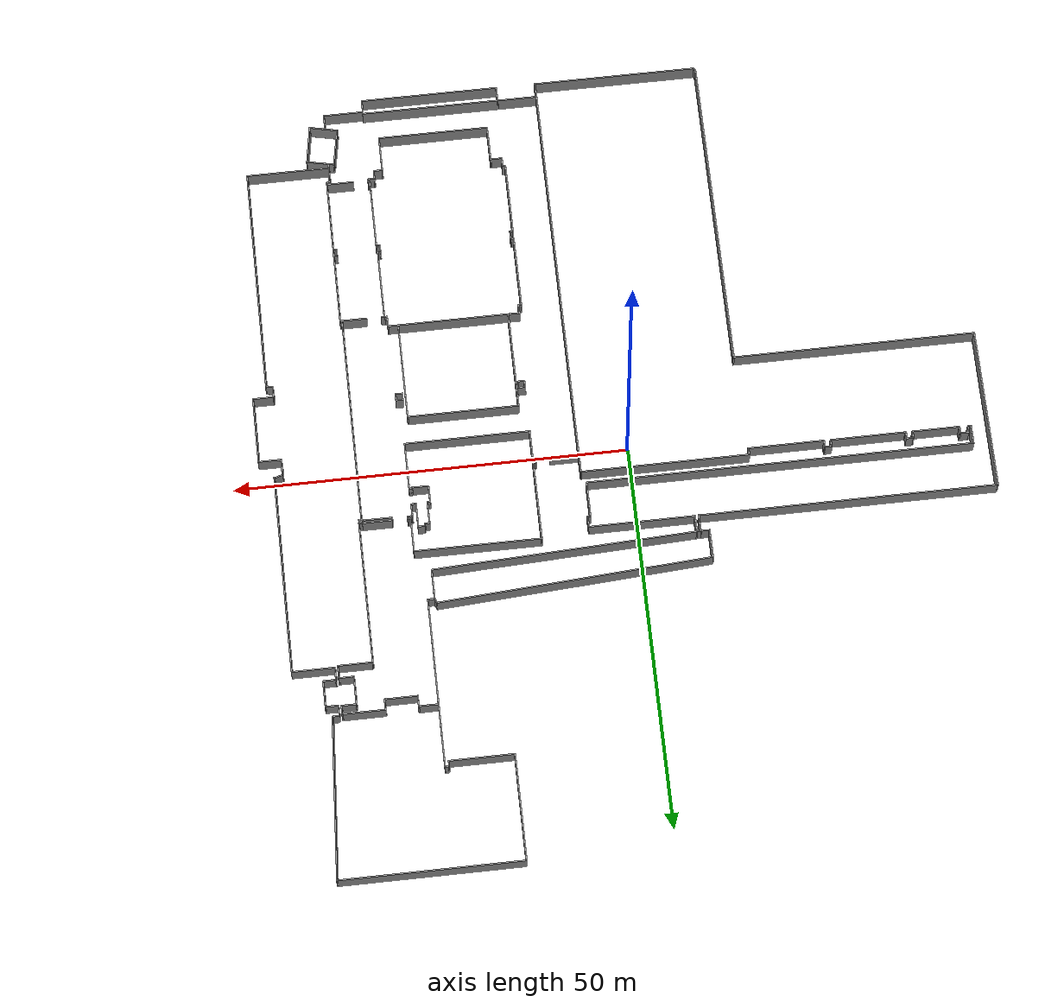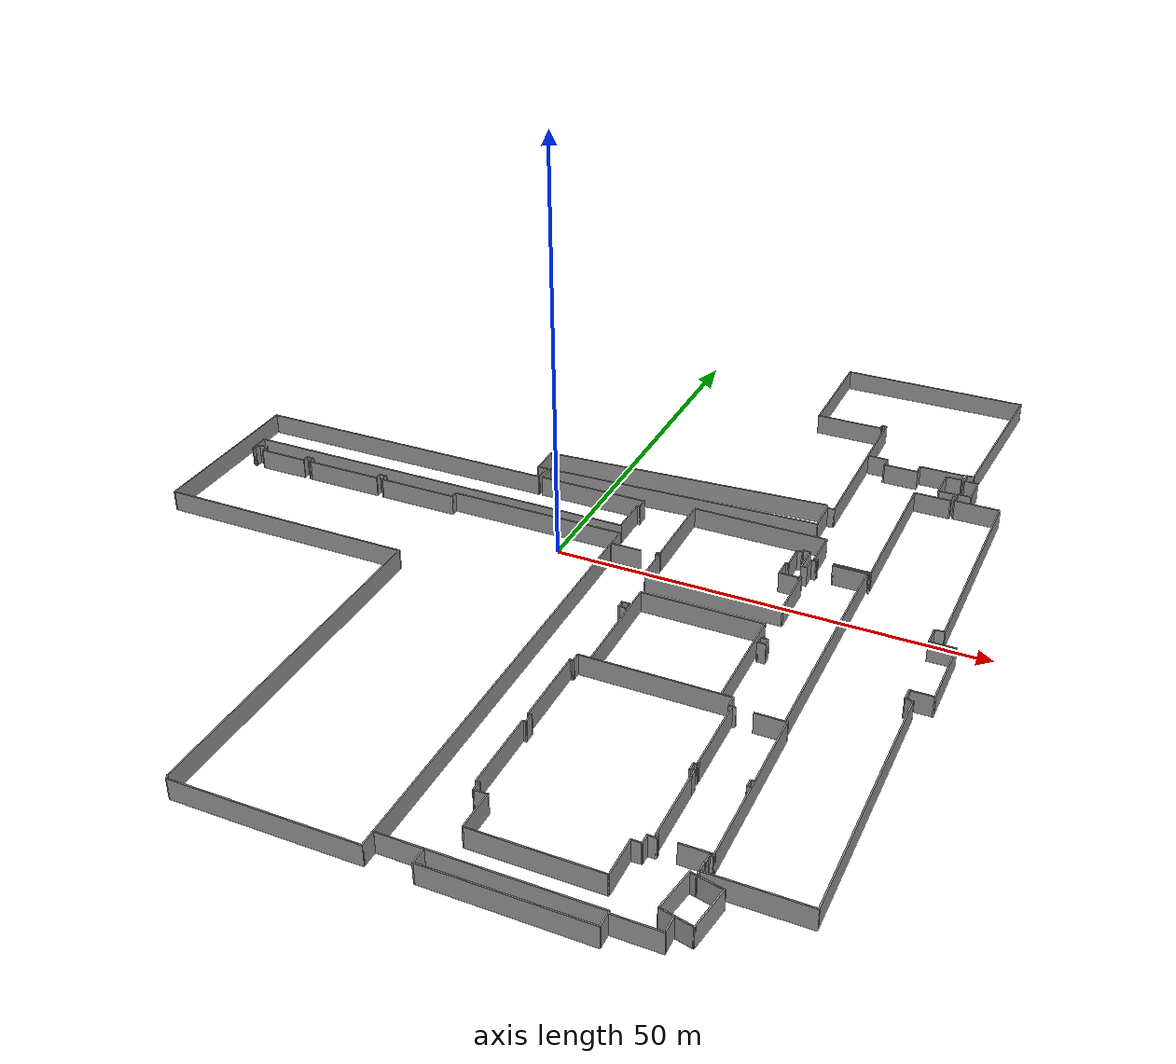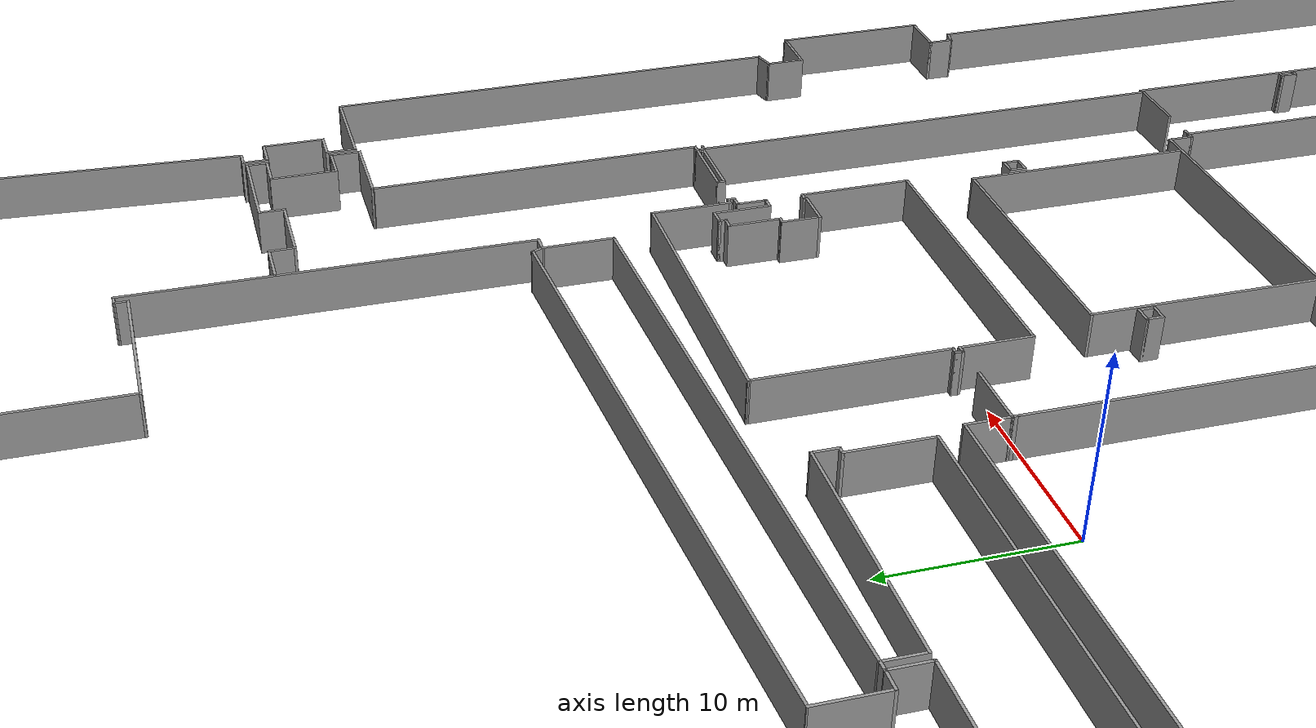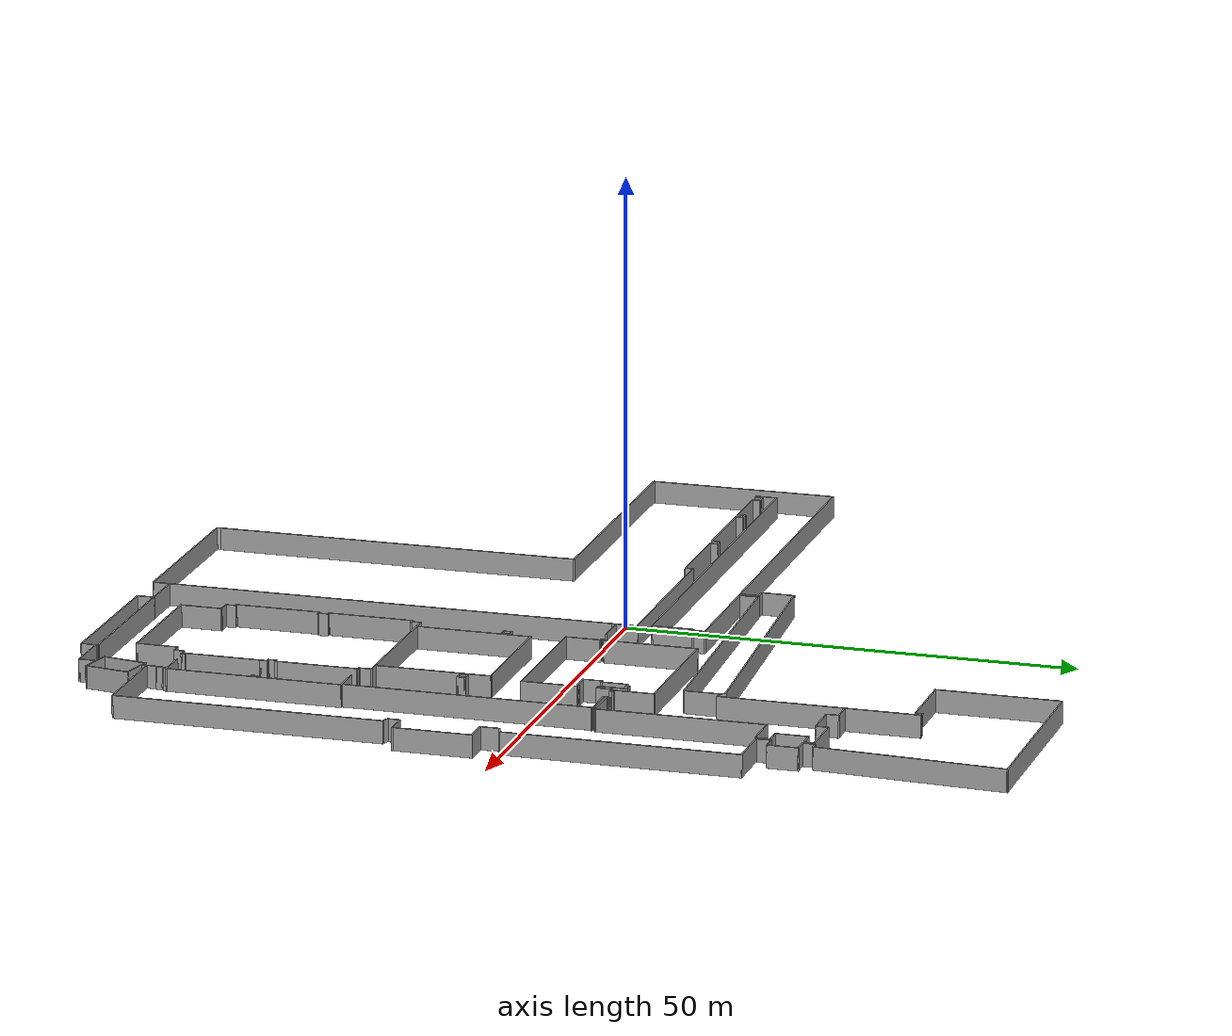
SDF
<?xml version='1.0'?>
<sdf version='1.6'>
  <model name='SEH_double_doors_open'>
    <pose frame=''>0.441181 0.582592 0 0 -0 0</pose>
    <link name='Wall_0'>
      <collision name='Wall_0_Collision'>
        <geometry>
          <box>
            <size>41 0.15 2.5</size>
          </box>
        </geometry>
        <pose frame=''>0 0 1.25 0 -0 0</pose>
      </collision>
      <visual name='Wall_0_Visual'>
        <pose frame=''>0 0 1.25 0 -0 0</pose>
        <geometry>
          <box>
            <size>41 0.15 2.5</size>
          </box>
        </geometry>
        <material>
          <script>
            <uri>file://media/materials/scripts/gazebo.material</uri>
            <name>Gazebo/Grey</name>
          </script>
          <ambient>1 1 1 1</ambient>
        </material>
        <meta>
          <layer>0</layer>
        </meta>
      </visual>
      <pose frame=''>-15.188 -31.31 0 0 -0 1.5708</pose>
    </link>
    <link name='Wall_1'>
      <collision name='Wall_1_Collision'>
        <geometry>
          <box>
            <size>31 0.15 2.5</size>
          </box>
        </geometry>
        <pose frame=''>0 0 1.25 0 -0 0</pose>
      </collision>
      <visual name='Wall_1_Visual'>
        <pose frame=''>0 0 1.25 0 -0 0</pose>
        <geometry>
          <box>
            <size>31 0.15 2.5</size>
          </box>
        </geometry>
        <material>
          <script>
            <uri>file://media/materials/scripts/gazebo.material</uri>
            <name>Gazebo/Grey</name>
          </script>
          <ambient>1 1 1 1</ambient>
        </material>
        <meta>
          <layer>0</layer>
        </meta>
      </visual>
      <pose frame=''>-30.613 -10.885 0 0 -0 3.14159</pose>
    </link>
    <link name='Wall_10'>
      <collision name='Wall_10_Collision'>
        <geometry>
          <box>
            <size>0.754811 0.15 2.5</size>
          </box>
        </geometry>
        <pose frame=''>0 0 1.25 0 -0 0</pose>
      </collision>
      <visual name='Wall_10_Visual'>
        <pose frame=''>0 0 1.25 0 -0 0</pose>
        <geometry>
          <box>
            <size>0.754811 0.15 2.5</size>
          </box>
        </geometry>
        <material>
          <script>
            <uri>file://media/materials/scripts/gazebo.material</uri>
            <name>Gazebo/Grey</name>
          </script>
          <ambient>1 1 1 1</ambient>
        </material>
        <meta>
          <layer>0</layer>
        </meta>
      </visual>
      <pose frame=''>25.6544 17.6654 0 0 -0 1.96559</pose>
    </link>
    <link name='Wall_101'>
      <collision name='Wall_101_Collision'>
        <geometry>
          <box>
            <size>19.75 0.15 2.5</size>
          </box>
        </geometry>
        <pose frame=''>0 0 1.25 0 -0 0</pose>
      </collision>
      <visual name='Wall_101_Visual'>
        <pose frame=''>0 0 1.25 0 -0 0</pose>
        <geometry>
          <box>
            <size>19.75 0.15 2.5</size>
          </box>
        </geometry>
        <material>
          <script>
            <uri>file://media/materials/scripts/gazebo.material</uri>
            <name>Gazebo/Grey</name>
          </script>
          <ambient>1 1 1 1</ambient>
        </material>
        <meta>
          <layer>0</layer>
        </meta>
      </visual>
      <pose frame=''>34.1091 -31.1312 0 0 -0 1.5708</pose>
    </link>
    <link name='Wall_103'>
      <collision name='Wall_103_Collision'>
        <geometry>
          <box>
            <size>3.5 0.15 2.5</size>
          </box>
        </geometry>
        <pose frame=''>0 0 1.25 0 -0 0</pose>
      </collision>
      <visual name='Wall_103_Visual'>
        <pose frame=''>0 0 1.25 0 -0 0</pose>
        <geometry>
          <box>
            <size>3.5 0.15 2.5</size>
          </box>
        </geometry>
        <material>
          <script>
            <uri>file://media/materials/scripts/gazebo.material</uri>
            <name>Gazebo/Grey</name>
          </script>
          <ambient>1 1 1 1</ambient>
        </material>
        <meta>
          <layer>0</layer>
        </meta>
      </visual>
      <pose frame=''>32.4341 -21.3312 0 0 -0 3.14159</pose>
    </link>
    <link name='Wall_105'>
      <collision name='Wall_105_Collision'>
        <geometry>
          <box>
            <size>0.5 0.15 2.5</size>
          </box>
        </geometry>
        <pose frame=''>0 0 1.25 0 -0 0</pose>
      </collision>
      <visual name='Wall_105_Visual'>
        <pose frame=''>0 0 1.25 0 -0 0</pose>
        <geometry>
          <box>
            <size>0.5 0.15 2.5</size>
          </box>
        </geometry>
        <material>
          <script>
            <uri>file://media/materials/scripts/gazebo.material</uri>
            <name>Gazebo/Grey</name>
          </script>
          <ambient>1 1 1 1</ambient>
        </material>
        <meta>
          <layer>0</layer>
        </meta>
      </visual>
      <pose frame=''>28.6395 -21.3021 0 0 -0 3.14159</pose>
    </link>
    <link name='Wall_106'>
      <collision name='Wall_106_Collision'>
        <geometry>
          <box>
            <size>9 0.15 2.5</size>
          </box>
        </geometry>
        <pose frame=''>0 0 1.25 0 -0 0</pose>
      </collision>
      <visual name='Wall_106_Visual'>
        <pose frame=''>0 0 1.25 0 -0 0</pose>
        <geometry>
          <box>
            <size>9 0.15 2.5</size>
          </box>
        </geometry>
        <material>
          <script>
            <uri>file://media/materials/scripts/gazebo.material</uri>
            <name>Gazebo/Grey</name>
          </script>
          <ambient>1 1 1 1</ambient>
        </material>
        <meta>
          <layer>0</layer>
        </meta>
      </visual>
      <pose frame=''>28.4645 -25.7271 0 0 0 -1.5708</pose>
    </link>
    <link name='Wall_109'>
      <collision name='Wall_109_Collision'>
        <geometry>
          <box>
            <size>0.5 0.15 2.5</size>
          </box>
        </geometry>
        <pose frame=''>0 0 1.25 0 -0 0</pose>
      </collision>
      <visual name='Wall_109_Visual'>
        <pose frame=''>0 0 1.25 0 -0 0</pose>
        <geometry>
          <box>
            <size>0.5 0.15 2.5</size>
          </box>
        </geometry>
        <material>
          <script>
            <uri>file://media/materials/scripts/gazebo.material</uri>
            <name>Gazebo/Grey</name>
          </script>
          <ambient>1 1 1 1</ambient>
        </material>
        <meta>
          <layer>0</layer>
        </meta>
      </visual>
      <pose frame=''>28.4645 -30.3271 0 0 0 -1.5708</pose>
    </link>
    <link name='Wall_110'>
      <collision name='Wall_110_Collision'>
        <geometry>
          <box>
            <size>0.5 0.15 2.5</size>
          </box>
        </geometry>
        <pose frame=''>0 0 1.25 0 -0 0</pose>
      </collision>
      <visual name='Wall_110_Visual'>
        <pose frame=''>0 0 1.25 0 -0 0</pose>
        <geometry>
          <box>
            <size>0.5 0.15 2.5</size>
          </box>
        </geometry>
        <material>
          <script>
            <uri>file://media/materials/scripts/gazebo.material</uri>
            <name>Gazebo/Grey</name>
          </script>
          <ambient>1 1 1 1</ambient>
        </material>
        <meta>
          <layer>0</layer>
        </meta>
      </visual>
      <pose frame=''>28.2895 -30.5021 0 0 -0 3.14159</pose>
    </link>
    <link name='Wall_111'>
      <collision name='Wall_111_Collision'>
        <geometry>
          <box>
            <size>1 0.15 2.5</size>
          </box>
        </geometry>
        <pose frame=''>0 0 1.25 0 -0 0</pose>
      </collision>
      <visual name='Wall_111_Visual'>
        <pose frame=''>0 0 1.25 0 -0 0</pose>
        <geometry>
          <box>
            <size>1 0.15 2.5</size>
          </box>
        </geometry>
        <material>
          <script>
            <uri>file://media/materials/scripts/gazebo.material</uri>
            <name>Gazebo/Grey</name>
          </script>
          <ambient>1 1 1 1</ambient>
        </material>
        <meta>
          <layer>0</layer>
        </meta>
      </visual>
      <pose frame=''>28.1145 -30.9271 0 0 0 -1.5708</pose>
    </link>
    <link name='Wall_112'>
      <collision name='Wall_112_Collision'>
        <geometry>
          <box>
            <size>0.5 0.15 2.5</size>
          </box>
        </geometry>
        <pose frame=''>0 0 1.25 0 -0 0</pose>
      </collision>
      <visual name='Wall_112_Visual'>
        <pose frame=''>0 0 1.25 0 -0 0</pose>
        <geometry>
          <box>
            <size>0.5 0.15 2.5</size>
          </box>
        </geometry>
        <material>
          <script>
            <uri>file://media/materials/scripts/gazebo.material</uri>
            <name>Gazebo/Grey</name>
          </script>
          <ambient>1 1 1 1</ambient>
        </material>
        <meta>
          <layer>0</layer>
        </meta>
      </visual>
      <pose frame=''>28.2895 -31.3521 0 0 -0 0</pose>
    </link>
    <link name='Wall_113'>
      <collision name='Wall_113_Collision'>
        <geometry>
          <box>
            <size>0.25 0.15 2.5</size>
          </box>
        </geometry>
        <pose frame=''>0 0 1.25 0 -0 0</pose>
      </collision>
      <visual name='Wall_113_Visual'>
        <pose frame=''>0 0 1.25 0 -0 0</pose>
        <geometry>
          <box>
            <size>0.25 0.15 2.5</size>
          </box>
        </geometry>
        <material>
          <script>
            <uri>file://media/materials/scripts/gazebo.material</uri>
            <name>Gazebo/Grey</name>
          </script>
          <ambient>1 1 1 1</ambient>
        </material>
        <meta>
          <layer>0</layer>
        </meta>
      </visual>
      <pose frame=''>28.5145 -31.3521 0 0 -0 0</pose>
    </link>
    <link name='Wall_114'>
      <collision name='Wall_114_Collision'>
        <geometry>
          <box>
            <size>0.931161 0.15 2.5</size>
          </box>
        </geometry>
        <pose frame=''>0 0 1.25 0 -0 0</pose>
      </collision>
      <visual name='Wall_114_Visual'>
        <pose frame=''>0 0 1.25 0 -0 0</pose>
        <geometry>
          <box>
            <size>0.931161 0.15 2.5</size>
          </box>
        </geometry>
        <material>
          <script>
            <uri>file://media/materials/scripts/gazebo.material</uri>
            <name>Gazebo/Grey</name>
          </script>
          <ambient>1 1 1 1</ambient>
        </material>
        <meta>
          <layer>0</layer>
        </meta>
      </visual>
      <pose frame=''>28.5648 -31.7427 0 0 0 -1.56992</pose>
    </link>
    <link name='Wall_116'>
      <collision name='Wall_116_Collision'>
        <geometry>
          <box>
            <size>0.5 0.15 2.5</size>
          </box>
        </geometry>
        <pose frame=''>0 0 1.25 0 -0 0</pose>
      </collision>
      <visual name='Wall_116_Visual'>
        <pose frame=''>0 0 1.25 0 -0 0</pose>
        <geometry>
          <box>
            <size>0.5 0.15 2.5</size>
          </box>
        </geometry>
        <material>
          <script>
            <uri>file://media/materials/scripts/gazebo.material</uri>
            <name>Gazebo/Grey</name>
          </script>
          <ambient>1 1 1 1</ambient>
        </material>
        <meta>
          <layer>0</layer>
        </meta>
      </visual>
      <pose frame=''>33.8845 -30.5093 0 0 -0 3.14159</pose>
    </link>
    <link name='Wall_117'>
      <collision name='Wall_117_Collision'>
        <geometry>
          <box>
            <size>1 0.15 2.5</size>
          </box>
        </geometry>
        <pose frame=''>0 0 1.25 0 -0 0</pose>
      </collision>
      <visual name='Wall_117_Visual'>
        <pose frame=''>0 0 1.25 0 -0 0</pose>
        <geometry>
          <box>
            <size>1 0.15 2.5</size>
          </box>
        </geometry>
        <material>
          <script>
            <uri>file://media/materials/scripts/gazebo.material</uri>
            <name>Gazebo/Grey</name>
          </script>
          <ambient>1 1 1 1</ambient>
        </material>
        <meta>
          <layer>0</layer>
        </meta>
      </visual>
      <pose frame=''>33.7095 -30.9343 0 0 0 -1.5708</pose>
    </link>
    <link name='Wall_118'>
      <collision name='Wall_118_Collision'>
        <geometry>
          <box>
            <size>0.5 0.15 2.5</size>
          </box>
        </geometry>
        <pose frame=''>0 0 1.25 0 -0 0</pose>
      </collision>
      <visual name='Wall_118_Visual'>
        <pose frame=''>0 0 1.25 0 -0 0</pose>
        <geometry>
          <box>
            <size>0.5 0.15 2.5</size>
          </box>
        </geometry>
        <material>
          <script>
            <uri>file://media/materials/scripts/gazebo.material</uri>
            <name>Gazebo/Grey</name>
          </script>
          <ambient>1 1 1 1</ambient>
        </material>
        <meta>
          <layer>0</layer>
        </meta>
      </visual>
      <pose frame=''>33.8845 -31.3593 0 0 -0 0</pose>
    </link>
    <link name='Wall_12'>
      <collision name='Wall_12_Collision'>
        <geometry>
          <box>
            <size>1 0.15 2.5</size>
          </box>
        </geometry>
        <pose frame=''>0 0 1.25 0 -0 0</pose>
      </collision>
      <visual name='Wall_12_Visual'>
        <pose frame=''>0 0 1.25 0 -0 0</pose>
        <geometry>
          <box>
            <size>1 0.15 2.5</size>
          </box>
        </geometry>
        <material>
          <script>
            <uri>file://media/materials/scripts/gazebo.material</uri>
            <name>Gazebo/Grey</name>
          </script>
          <ambient>1 1 1 1</ambient>
        </material>
        <meta>
          <layer>0</layer>
        </meta>
      </visual>
      <pose frame=''>26.1957 17.3863 0 0 -0 0</pose>
    </link>
    <link name='Wall_120'>
      <collision name='Wall_120_Collision'>
        <geometry>
          <box>
            <size>50.25 0.15 2.5</size>
          </box>
        </geometry>
        <pose frame=''>0 0 1.25 0 -0 0</pose>
      </collision>
      <visual name='Wall_120_Visual'>
        <pose frame=''>0 0 1.25 0 -0 0</pose>
        <geometry>
          <box>
            <size>50.25 0.15 2.5</size>
          </box>
        </geometry>
        <material>
          <script>
            <uri>file://media/materials/scripts/gazebo.material</uri>
            <name>Gazebo/Grey</name>
          </script>
          <ambient>1 1 1 1</ambient>
        </material>
        <meta>
          <layer>0</layer>
        </meta>
      </visual>
      <pose frame=''>5.8537 -25.2205 0 0 -0 1.5708</pose>
    </link>
    <link name='Wall_122'>
      <collision name='Wall_122_Collision'>
        <geometry>
          <box>
            <size>0.5 0.15 2.5</size>
          </box>
        </geometry>
        <pose frame=''>0 0 1.25 0 -0 0</pose>
      </collision>
      <visual name='Wall_122_Visual'>
        <pose frame=''>0 0 1.25 0 -0 0</pose>
        <geometry>
          <box>
            <size>0.5 0.15 2.5</size>
          </box>
        </geometry>
        <material>
          <script>
            <uri>file://media/materials/scripts/gazebo.material</uri>
            <name>Gazebo/Grey</name>
          </script>
          <ambient>1 1 1 1</ambient>
        </material>
        <meta>
          <layer>0</layer>
        </meta>
      </visual>
      <pose frame=''>5.8537 0.004461 0 0 -0 1.5708</pose>
    </link>
    <link name='Wall_123'>
      <collision name='Wall_123_Collision'>
        <geometry>
          <box>
            <size>3.75 0.15 2.5</size>
          </box>
        </geometry>
        <pose frame=''>0 0 1.25 0 -0 0</pose>
      </collision>
      <visual name='Wall_123_Visual'>
        <pose frame=''>0 0 1.25 0 -0 0</pose>
        <geometry>
          <box>
            <size>3.75 0.15 2.5</size>
          </box>
        </geometry>
        <material>
          <script>
            <uri>file://media/materials/scripts/gazebo.material</uri>
            <name>Gazebo/Grey</name>
          </script>
          <ambient>1 1 1 1</ambient>
        </material>
        <meta>
          <layer>0</layer>
        </meta>
      </visual>
      <pose frame=''>7.6537 0.179461 0 0 -0 0</pose>
    </link>
    <link name='Wall_125'>
      <collision name='Wall_125_Collision'>
        <geometry>
          <box>
            <size>0.5 0.15 2.5</size>
          </box>
        </geometry>
        <pose frame=''>0 0 1.25 0 -0 0</pose>
      </collision>
      <visual name='Wall_125_Visual'>
        <pose frame=''>0 0 1.25 0 -0 0</pose>
        <geometry>
          <box>
            <size>0.5 0.15 2.5</size>
          </box>
        </geometry>
        <material>
          <script>
            <uri>file://media/materials/scripts/gazebo.material</uri>
            <name>Gazebo/Grey</name>
          </script>
          <ambient>1 1 1 1</ambient>
        </material>
        <meta>
          <layer>0</layer>
        </meta>
      </visual>
      <pose frame=''>11.5048 0.195336 0 0 -0 0</pose>
    </link>
    <link name='Wall_126'>
      <collision name='Wall_126_Collision'>
        <geometry>
          <box>
            <size>4 0.15 2.5</size>
          </box>
        </geometry>
        <pose frame=''>0 0 1.25 0 -0 0</pose>
      </collision>
      <visual name='Wall_126_Visual'>
        <pose frame=''>0 0 1.25 0 -0 0</pose>
        <geometry>
          <box>
            <size>4 0.15 2.5</size>
          </box>
        </geometry>
        <material>
          <script>
            <uri>file://media/materials/scripts/gazebo.material</uri>
            <name>Gazebo/Grey</name>
          </script>
          <ambient>1 1 1 1</ambient>
        </material>
        <meta>
          <layer>0</layer>
        </meta>
      </visual>
      <pose frame=''>11.6798 -1.72966 0 0 0 -1.5708</pose>
    </link>
    <link name='Wall_127'>
      <collision name='Wall_127_Collision'>
        <geometry>
          <box>
            <size>16 0.15 2.5</size>
          </box>
        </geometry>
        <pose frame=''>0 0 1.25 0 -0 0</pose>
      </collision>
      <visual name='Wall_127_Visual'>
        <pose frame=''>0 0 1.25 0 -0 0</pose>
        <geometry>
          <box>
            <size>16 0.15 2.5</size>
          </box>
        </geometry>
        <material>
          <script>
            <uri>file://media/materials/scripts/gazebo.material</uri>
            <name>Gazebo/Grey</name>
          </script>
          <ambient>1 1 1 1</ambient>
        </material>
        <meta>
          <layer>0</layer>
        </meta>
      </visual>
      <pose frame=''>19.6048 -3.65466 0 0 -0 0</pose>
    </link>
    <link name='Wall_128'>
      <collision name='Wall_128_Collision'>
        <geometry>
          <box>
            <size>6.25 0.15 2.5</size>
          </box>
        </geometry>
        <pose frame=''>0 0 1.25 0 -0 0</pose>
      </collision>
      <visual name='Wall_128_Visual'>
        <pose frame=''>0 0 1.25 0 -0 0</pose>
        <geometry>
          <box>
            <size>6.25 0.15 2.5</size>
          </box>
        </geometry>
        <material>
          <script>
            <uri>file://media/materials/scripts/gazebo.material</uri>
            <name>Gazebo/Grey</name>
          </script>
          <ambient>1 1 1 1</ambient>
        </material>
        <meta>
          <layer>0</layer>
        </meta>
      </visual>
      <pose frame=''>27.5298 -0.604664 0 0 -0 1.5708</pose>
    </link>
    <link name='Wall_129'>
      <collision name='Wall_129_Collision'>
        <geometry>
          <box>
            <size>0.5 0.15 2.5</size>
          </box>
        </geometry>
        <pose frame=''>0 0 1.25 0 -0 0</pose>
      </collision>
      <visual name='Wall_129_Visual'>
        <pose frame=''>0 0 1.25 0 -0 0</pose>
        <geometry>
          <box>
            <size>0.5 0.15 2.5</size>
          </box>
        </geometry>
        <material>
          <script>
            <uri>file://media/materials/scripts/gazebo.material</uri>
            <name>Gazebo/Grey</name>
          </script>
          <ambient>1 1 1 1</ambient>
        </material>
        <meta>
          <layer>0</layer>
        </meta>
      </visual>
      <pose frame=''>27.3548 2.44534 0 0 -0 3.14159</pose>
    </link>
    <link name='Wall_13'>
      <collision name='Wall_13_Collision'>
        <geometry>
          <box>
            <size>22 0.15 2.5</size>
          </box>
        </geometry>
        <pose frame=''>0 0 1.25 0 -0 0</pose>
      </collision>
      <visual name='Wall_13_Visual'>
        <pose frame=''>0 0 1.25 0 -0 0</pose>
        <geometry>
          <box>
            <size>22 0.15 2.5</size>
          </box>
        </geometry>
        <material>
          <script>
            <uri>file://media/materials/scripts/gazebo.material</uri>
            <name>Gazebo/Grey</name>
          </script>
          <ambient>1 1 1 1</ambient>
        </material>
        <meta>
          <layer>0</layer>
        </meta>
      </visual>
      <pose frame=''>26.6207 28.3113 0 0 -0 1.5708</pose>
    </link>
    <link name='Wall_133'>
      <collision name='Wall_133_Collision'>
        <geometry>
          <box>
            <size>0.25 0.15 2.5</size>
          </box>
        </geometry>
        <pose frame=''>0 0 1.25 0 -0 0</pose>
      </collision>
      <visual name='Wall_133_Visual'>
        <pose frame=''>0 0 1.25 0 -0 0</pose>
        <geometry>
          <box>
            <size>0.25 0.15 2.5</size>
          </box>
        </geometry>
        <material>
          <script>
            <uri>file://media/materials/scripts/gazebo.material</uri>
            <name>Gazebo/Grey</name>
          </script>
          <ambient>1 1 1 1</ambient>
        </material>
        <meta>
          <layer>0</layer>
        </meta>
      </visual>
      <pose frame=''>27.1798 2.39534 0 0 0 -1.5708</pose>
    </link>
    <link name='Wall_134'>
      <collision name='Wall_134_Collision'>
        <geometry>
          <box>
            <size>2.25 0.15 2.5</size>
          </box>
        </geometry>
        <pose frame=''>0 0 1.25 0 -0 0</pose>
      </collision>
      <visual name='Wall_134_Visual'>
        <pose frame=''>0 0 1.25 0 -0 0</pose>
        <geometry>
          <box>
            <size>2.25 0.15 2.5</size>
          </box>
        </geometry>
        <material>
          <script>
            <uri>file://media/materials/scripts/gazebo.material</uri>
            <name>Gazebo/Grey</name>
          </script>
          <ambient>1 1 1 1</ambient>
        </material>
        <meta>
          <layer>0</layer>
        </meta>
      </visual>
      <pose frame=''>26.1298 2.34534 0 0 -0 3.14159</pose>
    </link>
    <link name='Wall_135'>
      <collision name='Wall_135_Collision'>
        <geometry>
          <box>
            <size>2.25 0.15 2.5</size>
          </box>
        </geometry>
        <pose frame=''>0 0 1.25 0 -0 0</pose>
      </collision>
      <visual name='Wall_135_Visual'>
        <pose frame=''>0 0 1.25 0 -0 0</pose>
        <geometry>
          <box>
            <size>2.25 0.15 2.5</size>
          </box>
        </geometry>
        <material>
          <script>
            <uri>file://media/materials/scripts/gazebo.material</uri>
            <name>Gazebo/Grey</name>
          </script>
          <ambient>1 1 1 1</ambient>
        </material>
        <meta>
          <layer>0</layer>
        </meta>
      </visual>
      <pose frame=''>25.0798 3.39534 0 0 -0 1.5708</pose>
    </link>
    <link name='Wall_136'>
      <collision name='Wall_136_Collision'>
        <geometry>
          <box>
            <size>0.5 0.15 2.5</size>
          </box>
        </geometry>
        <pose frame=''>0 0 1.25 0 -0 0</pose>
      </collision>
      <visual name='Wall_136_Visual'>
        <pose frame=''>0 0 1.25 0 -0 0</pose>
        <geometry>
          <box>
            <size>0.5 0.15 2.5</size>
          </box>
        </geometry>
        <material>
          <script>
            <uri>file://media/materials/scripts/gazebo.material</uri>
            <name>Gazebo/Grey</name>
          </script>
          <ambient>1 1 1 1</ambient>
        </material>
        <meta>
          <layer>0</layer>
        </meta>
      </visual>
      <pose frame=''>25.2548 4.44534 0 0 -0 0</pose>
    </link>
    <link name='Wall_137'>
      <collision name='Wall_137_Collision'>
        <geometry>
          <box>
            <size>3 0.15 2.5</size>
          </box>
        </geometry>
        <pose frame=''>0 0 1.25 0 -0 0</pose>
      </collision>
      <visual name='Wall_137_Visual'>
        <pose frame=''>0 0 1.25 0 -0 0</pose>
        <geometry>
          <box>
            <size>3 0.15 2.5</size>
          </box>
        </geometry>
        <material>
          <script>
            <uri>file://media/materials/scripts/gazebo.material</uri>
            <name>Gazebo/Grey</name>
          </script>
          <ambient>1 1 1 1</ambient>
        </material>
        <meta>
          <layer>0</layer>
        </meta>
      </visual>
      <pose frame=''>25.4298 5.87034 0 0 -0 1.5708</pose>
    </link>
    <link name='Wall_138'>
      <collision name='Wall_138_Collision'>
        <geometry>
          <box>
            <size>0.75 0.15 2.5</size>
          </box>
        </geometry>
        <pose frame=''>0 0 1.25 0 -0 0</pose>
      </collision>
      <visual name='Wall_138_Visual'>
        <pose frame=''>0 0 1.25 0 -0 0</pose>
        <geometry>
          <box>
            <size>0.75 0.15 2.5</size>
          </box>
        </geometry>
        <material>
          <script>
            <uri>file://media/materials/scripts/gazebo.material</uri>
            <name>Gazebo/Grey</name>
          </script>
          <ambient>1 1 1 1</ambient>
        </material>
        <meta>
          <layer>0</layer>
        </meta>
      </visual>
      <pose frame=''>25.7298 7.29534 0 0 -0 0</pose>
    </link>
    <link name='Wall_143'>
      <collision name='Wall_143_Collision'>
        <geometry>
          <box>
            <size>0.5 0.15 2.5</size>
          </box>
        </geometry>
        <pose frame=''>0 0 1.25 0 -0 0</pose>
      </collision>
      <visual name='Wall_143_Visual'>
        <pose frame=''>0 0 1.25 0 -0 0</pose>
        <geometry>
          <box>
            <size>0.5 0.15 2.5</size>
          </box>
        </geometry>
        <material>
          <script>
            <uri>file://media/materials/scripts/gazebo.material</uri>
            <name>Gazebo/Grey</name>
          </script>
          <ambient>1 1 1 1</ambient>
        </material>
        <meta>
          <layer>0</layer>
        </meta>
      </visual>
      <pose frame=''>26.0298 7.47034 0 0 -0 1.5708</pose>
    </link>
    <link name='Wall_144'>
      <collision name='Wall_144_Collision'>
        <geometry>
          <box>
            <size>1 0.15 2.5</size>
          </box>
        </geometry>
        <pose frame=''>0 0 1.25 0 -0 0</pose>
      </collision>
      <visual name='Wall_144_Visual'>
        <pose frame=''>0 0 1.25 0 -0 0</pose>
        <geometry>
          <box>
            <size>1 0.15 2.5</size>
          </box>
        </geometry>
        <material>
          <script>
            <uri>file://media/materials/scripts/gazebo.material</uri>
            <name>Gazebo/Grey</name>
          </script>
          <ambient>1 1 1 1</ambient>
        </material>
        <meta>
          <layer>0</layer>
        </meta>
      </visual>
      <pose frame=''>26.4548 7.64534 0 0 -0 0</pose>
    </link>
    <link name='Wall_145'>
      <collision name='Wall_145_Collision'>
        <geometry>
          <box>
            <size>3.25 0.15 2.5</size>
          </box>
        </geometry>
        <pose frame=''>0 0 1.25 0 -0 0</pose>
      </collision>
      <visual name='Wall_145_Visual'>
        <pose frame=''>0 0 1.25 0 -0 0</pose>
        <geometry>
          <box>
            <size>3.25 0.15 2.5</size>
          </box>
        </geometry>
        <material>
          <script>
            <uri>file://media/materials/scripts/gazebo.material</uri>
            <name>Gazebo/Grey</name>
          </script>
          <ambient>1 1 1 1</ambient>
        </material>
        <meta>
          <layer>0</layer>
        </meta>
      </visual>
      <pose frame=''>26.8798 6.09534 0 0 0 -1.5708</pose>
    </link>
    <link name='Wall_146'>
      <collision name='Wall_146_Collision'>
        <geometry>
          <box>
            <size>0.75 0.15 2.5</size>
          </box>
        </geometry>
        <pose frame=''>0 0 1.25 0 -0 0</pose>
      </collision>
      <visual name='Wall_146_Visual'>
        <pose frame=''>0 0 1.25 0 -0 0</pose>
        <geometry>
          <box>
            <size>0.75 0.15 2.5</size>
          </box>
        </geometry>
        <material>
          <script>
            <uri>file://media/materials/scripts/gazebo.material</uri>
            <name>Gazebo/Grey</name>
          </script>
          <ambient>1 1 1 1</ambient>
        </material>
        <meta>
          <layer>0</layer>
        </meta>
      </visual>
      <pose frame=''>27.1798 4.54534 0 0 -0 0</pose>
    </link>
    <link name='Wall_147'>
      <collision name='Wall_147_Collision'>
        <geometry>
          <box>
            <size>1.75 0.15 2.5</size>
          </box>
        </geometry>
        <pose frame=''>0 0 1.25 0 -0 0</pose>
      </collision>
      <visual name='Wall_147_Visual'>
        <pose frame=''>0 0 1.25 0 -0 0</pose>
        <geometry>
          <box>
            <size>1.75 0.15 2.5</size>
          </box>
        </geometry>
        <material>
          <script>
            <uri>file://media/materials/scripts/gazebo.material</uri>
            <name>Gazebo/Grey</name>
          </script>
          <ambient>1 1 1 1</ambient>
        </material>
        <meta>
          <layer>0</layer>
        </meta>
      </visual>
      <pose frame=''>27.4798 5.34534 0 0 -0 1.5708</pose>
    </link>
    <link name='Wall_148'>
      <collision name='Wall_148_Collision'>
        <geometry>
          <box>
            <size>0.75 0.15 2.5</size>
          </box>
        </geometry>
        <pose frame=''>0 0 1.25 0 -0 0</pose>
      </collision>
      <visual name='Wall_148_Visual'>
        <pose frame=''>0 0 1.25 0 -0 0</pose>
        <geometry>
          <box>
            <size>0.75 0.15 2.5</size>
          </box>
        </geometry>
        <material>
          <script>
            <uri>file://media/materials/scripts/gazebo.material</uri>
            <name>Gazebo/Grey</name>
          </script>
          <ambient>1 1 1 1</ambient>
        </material>
        <meta>
          <layer>0</layer>
        </meta>
      </visual>
      <pose frame=''>27.7798 6.14534 0 0 -0 0</pose>
    </link>
    <link name='Wall_150'>
      <collision name='Wall_150_Collision'>
        <geometry>
          <box>
            <size>4 0.15 2.5</size>
          </box>
        </geometry>
        <pose frame=''>0 0 1.25 0 -0 0</pose>
      </collision>
      <visual name='Wall_150_Visual'>
        <pose frame=''>0 0 1.25 0 -0 0</pose>
        <geometry>
          <box>
            <size>4 0.15 2.5</size>
          </box>
        </geometry>
        <material>
          <script>
            <uri>file://media/materials/scripts/gazebo.material</uri>
            <name>Gazebo/Grey</name>
          </script>
          <ambient>1 1 1 1</ambient>
        </material>
        <meta>
          <layer>0</layer>
        </meta>
      </visual>
      <pose frame=''>31.9514 6.07094 0 0 -0 0</pose>
    </link>
    <link name='Wall_151'>
      <collision name='Wall_151_Collision'>
        <geometry>
          <box>
            <size>27.5 0.15 2.5</size>
          </box>
        </geometry>
        <pose frame=''>0 0 1.25 0 -0 0</pose>
      </collision>
      <visual name='Wall_151_Visual'>
        <pose frame=''>0 0 1.25 0 -0 0</pose>
        <geometry>
          <box>
            <size>27.5 0.15 2.5</size>
          </box>
        </geometry>
        <material>
          <script>
            <uri>file://media/materials/scripts/gazebo.material</uri>
            <name>Gazebo/Grey</name>
          </script>
          <ambient>1 1 1 1</ambient>
        </material>
        <meta>
          <layer>0</layer>
        </meta>
      </visual>
      <pose frame=''>33.8764 -7.60406 0 0 0 -1.5708</pose>
    </link>
    <link name='Wall_156'>
      <collision name='Wall_156_Collision'>
        <geometry>
          <box>
            <size>0.5 0.15 2.5</size>
          </box>
        </geometry>
        <pose frame=''>0 0 1.25 0 -0 0</pose>
      </collision>
      <visual name='Wall_156_Visual'>
        <pose frame=''>0 0 1.25 0 -0 0</pose>
        <geometry>
          <box>
            <size>0.5 0.15 2.5</size>
          </box>
        </geometry>
        <material>
          <script>
            <uri>file://media/materials/scripts/gazebo.material</uri>
            <name>Gazebo/Grey</name>
          </script>
          <ambient>1 1 1 1</ambient>
        </material>
        <meta>
          <layer>0</layer>
        </meta>
      </visual>
      <pose frame=''>28.2895 -21.3021 0 0 -0 3.14159</pose>
    </link>
    <link name='Wall_157'>
      <collision name='Wall_157_Collision'>
        <geometry>
          <box>
            <size>1.5 0.15 2.5</size>
          </box>
        </geometry>
        <pose frame=''>0 0 1.25 0 -0 0</pose>
      </collision>
      <visual name='Wall_157_Visual'>
        <pose frame=''>0 0 1.25 0 -0 0</pose>
        <geometry>
          <box>
            <size>1.5 0.15 2.5</size>
          </box>
        </geometry>
        <material>
          <script>
            <uri>file://media/materials/scripts/gazebo.material</uri>
            <name>Gazebo/Grey</name>
          </script>
          <ambient>1 1 1 1</ambient>
        </material>
        <meta>
          <layer>0</layer>
        </meta>
      </visual>
      <pose frame=''>28.1145 -20.6271 0 0 -0 1.5708</pose>
    </link>
    <link name='Wall_158'>
      <collision name='Wall_158_Collision'>
        <geometry>
          <box>
            <size>17 0.15 2.5</size>
          </box>
        </geometry>
        <pose frame=''>0 0 1.25 0 -0 0</pose>
      </collision>
      <visual name='Wall_158_Visual'>
        <pose frame=''>0 0 1.25 0 -0 0</pose>
        <geometry>
          <box>
            <size>17 0.15 2.5</size>
          </box>
        </geometry>
        <material>
          <script>
            <uri>file://media/materials/scripts/gazebo.material</uri>
            <name>Gazebo/Grey</name>
          </script>
          <ambient>1 1 1 1</ambient>
        </material>
        <meta>
          <layer>0</layer>
        </meta>
      </visual>
      <pose frame=''>19.6895 -19.9521 0 0 -0 3.14159</pose>
    </link>
    <link name='Wall_159'>
      <collision name='Wall_159_Collision'>
        <geometry>
          <box>
            <size>1.25 0.15 2.5</size>
          </box>
        </geometry>
        <pose frame=''>0 0 1.25 0 -0 0</pose>
      </collision>
      <visual name='Wall_159_Visual'>
        <pose frame=''>0 0 1.25 0 -0 0</pose>
        <geometry>
          <box>
            <size>1.25 0.15 2.5</size>
          </box>
        </geometry>
        <material>
          <script>
            <uri>file://media/materials/scripts/gazebo.material</uri>
            <name>Gazebo/Grey</name>
          </script>
          <ambient>1 1 1 1</ambient>
        </material>
        <meta>
          <layer>0</layer>
        </meta>
      </visual>
      <pose frame=''>11.2645 -20.5021 0 0 0 -1.5708</pose>
    </link>
    <link name='Wall_160'>
      <collision name='Wall_160_Collision'>
        <geometry>
          <box>
            <size>0.5 0.15 2.5</size>
          </box>
        </geometry>
        <pose frame=''>0 0 1.25 0 -0 0</pose>
      </collision>
      <visual name='Wall_160_Visual'>
        <pose frame=''>0 0 1.25 0 -0 0</pose>
        <geometry>
          <box>
            <size>0.5 0.15 2.5</size>
          </box>
        </geometry>
        <material>
          <script>
            <uri>file://media/materials/scripts/gazebo.material</uri>
            <name>Gazebo/Grey</name>
          </script>
          <ambient>1 1 1 1</ambient>
        </material>
        <meta>
          <layer>0</layer>
        </meta>
      </visual>
      <pose frame=''>11.0895 -21.0521 0 0 -0 3.14159</pose>
    </link>
    <link name='Wall_161'>
      <collision name='Wall_161_Collision'>
        <geometry>
          <box>
            <size>9.5 0.15 2.5</size>
          </box>
        </geometry>
        <pose frame=''>0 0 1.25 0 -0 0</pose>
      </collision>
      <visual name='Wall_161_Visual'>
        <pose frame=''>0 0 1.25 0 -0 0</pose>
        <geometry>
          <box>
            <size>9.5 0.15 2.5</size>
          </box>
        </geometry>
        <material>
          <script>
            <uri>file://media/materials/scripts/gazebo.material</uri>
            <name>Gazebo/Grey</name>
          </script>
          <ambient>1 1 1 1</ambient>
        </material>
        <meta>
          <layer>0</layer>
        </meta>
      </visual>
      <pose frame=''>10.9145 -25.7271 0 0 0 -1.5708</pose>
    </link>
    <link name='Wall_163'>
      <collision name='Wall_163_Collision'>
        <geometry>
          <box>
            <size>0.5 0.15 2.5</size>
          </box>
        </geometry>
        <pose frame=''>0 0 1.25 0 -0 0</pose>
      </collision>
      <visual name='Wall_163_Visual'>
        <pose frame=''>0 0 1.25 0 -0 0</pose>
        <geometry>
          <box>
            <size>0.5 0.15 2.5</size>
          </box>
        </geometry>
        <material>
          <script>
            <uri>file://media/materials/scripts/gazebo.material</uri>
            <name>Gazebo/Grey</name>
          </script>
          <ambient>1 1 1 1</ambient>
        </material>
        <meta>
          <layer>0</layer>
        </meta>
      </visual>
      <pose frame=''>11.0895 -30.4021 0 0 -0 0</pose>
    </link>
    <link name='Wall_164'>
      <collision name='Wall_164_Collision'>
        <geometry>
          <box>
            <size>1.25 0.15 2.5</size>
          </box>
        </geometry>
        <pose frame=''>0 0 1.25 0 -0 0</pose>
      </collision>
      <visual name='Wall_164_Visual'>
        <pose frame=''>0 0 1.25 0 -0 0</pose>
        <geometry>
          <box>
            <size>1.25 0.15 2.5</size>
          </box>
        </geometry>
        <material>
          <script>
            <uri>file://media/materials/scripts/gazebo.material</uri>
            <name>Gazebo/Grey</name>
          </script>
          <ambient>1 1 1 1</ambient>
        </material>
        <meta>
          <layer>0</layer>
        </meta>
      </visual>
      <pose frame=''>11.2645 -30.9521 0 0 0 -1.5708</pose>
    </link>
    <link name='Wall_165'>
      <collision name='Wall_165_Collision'>
        <geometry>
          <box>
            <size>0.5 0.15 2.5</size>
          </box>
        </geometry>
        <pose frame=''>0 0 1.25 0 -0 0</pose>
      </collision>
      <visual name='Wall_165_Visual'>
        <pose frame=''>0 0 1.25 0 -0 0</pose>
        <geometry>
          <box>
            <size>0.5 0.15 2.5</size>
          </box>
        </geometry>
        <material>
          <script>
            <uri>file://media/materials/scripts/gazebo.material</uri>
            <name>Gazebo/Grey</name>
          </script>
          <ambient>1 1 1 1</ambient>
        </material>
        <meta>
          <layer>0</layer>
        </meta>
      </visual>
      <pose frame=''>11.0895 -31.5021 0 0 -0 3.14159</pose>
    </link>
    <link name='Wall_166'>
      <collision name='Wall_166_Collision'>
        <geometry>
          <box>
            <size>9.5 0.15 2.5</size>
          </box>
        </geometry>
        <pose frame=''>0 0 1.25 0 -0 0</pose>
      </collision>
      <visual name='Wall_166_Visual'>
        <pose frame=''>0 0 1.25 0 -0 0</pose>
        <geometry>
          <box>
            <size>9.5 0.15 2.5</size>
          </box>
        </geometry>
        <material>
          <script>
            <uri>file://media/materials/scripts/gazebo.material</uri>
            <name>Gazebo/Grey</name>
          </script>
          <ambient>1 1 1 1</ambient>
        </material>
        <meta>
          <layer>0</layer>
        </meta>
      </visual>
      <pose frame=''>10.9145 -36.1771 0 0 0 -1.5708</pose>
    </link>
    <link name='Wall_167'>
      <collision name='Wall_167_Collision'>
        <geometry>
          <box>
            <size>0.5 0.15 2.5</size>
          </box>
        </geometry>
        <pose frame=''>0 0 1.25 0 -0 0</pose>
      </collision>
      <visual name='Wall_167_Visual'>
        <pose frame=''>0 0 1.25 0 -0 0</pose>
        <geometry>
          <box>
            <size>0.5 0.15 2.5</size>
          </box>
        </geometry>
        <material>
          <script>
            <uri>file://media/materials/scripts/gazebo.material</uri>
            <name>Gazebo/Grey</name>
          </script>
          <ambient>1 1 1 1</ambient>
        </material>
        <meta>
          <layer>0</layer>
        </meta>
      </visual>
      <pose frame=''>11.0895 -40.8521 0 0 -0 0</pose>
    </link>
    <link name='Wall_168'>
      <collision name='Wall_168_Collision'>
        <geometry>
          <box>
            <size>1.25 0.15 2.5</size>
          </box>
        </geometry>
        <pose frame=''>0 0 1.25 0 -0 0</pose>
      </collision>
      <visual name='Wall_168_Visual'>
        <pose frame=''>0 0 1.25 0 -0 0</pose>
        <geometry>
          <box>
            <size>1.25 0.15 2.5</size>
          </box>
        </geometry>
        <material>
          <script>
            <uri>file://media/materials/scripts/gazebo.material</uri>
            <name>Gazebo/Grey</name>
          </script>
          <ambient>1 1 1 1</ambient>
        </material>
        <meta>
          <layer>0</layer>
        </meta>
      </visual>
      <pose frame=''>11.2645 -41.4021 0 0 0 -1.5708</pose>
    </link>
    <link name='Wall_169'>
      <collision name='Wall_169_Collision'>
        <geometry>
          <box>
            <size>1.60081 0.15 2.5</size>
          </box>
        </geometry>
        <pose frame=''>0 0 1.25 0 -0 0</pose>
      </collision>
      <visual name='Wall_169_Visual'>
        <pose frame=''>0 0 1.25 0 -0 0</pose>
        <geometry>
          <box>
            <size>1.60081 0.15 2.5</size>
          </box>
        </geometry>
        <material>
          <script>
            <uri>file://media/materials/scripts/gazebo.material</uri>
            <name>Gazebo/Grey</name>
          </script>
          <ambient>1 1 1 1</ambient>
        </material>
        <meta>
          <layer>0</layer>
        </meta>
      </visual>
      <pose frame=''>11.9898 -41.9427 0 0 -0 0.012986</pose>
    </link>
    <link name='Wall_17'>
      <collision name='Wall_17_Collision'>
        <geometry>
          <box>
            <size>8.3246 0.15 2.5</size>
          </box>
        </geometry>
        <pose frame=''>0 0 1.25 0 -0 0</pose>
      </collision>
      <visual name='Wall_17_Visual'>
        <pose frame=''>0 0 1.25 0 -0 0</pose>
        <geometry>
          <box>
            <size>8.3246 0.15 2.5</size>
          </box>
        </geometry>
        <material>
          <script>
            <uri>file://media/materials/scripts/gazebo.material</uri>
            <name>Gazebo/Grey</name>
          </script>
          <ambient>1 1 1 1</ambient>
        </material>
        <meta>
          <layer>0</layer>
        </meta>
      </visual>
      <pose frame=''>22.0285 38.5432 0 0 0 -3.14119</pose>
    </link>
    <link name='Wall_171'>
      <collision name='Wall_171_Collision'>
        <geometry>
          <box>
            <size>12.75 0.15 2.5</size>
          </box>
        </geometry>
        <pose frame=''>0 0 1.25 0 -0 0</pose>
      </collision>
      <visual name='Wall_171_Visual'>
        <pose frame=''>0 0 1.25 0 -0 0</pose>
        <geometry>
          <box>
            <size>12.75 0.15 2.5</size>
          </box>
        </geometry>
        <material>
          <script>
            <uri>file://media/materials/scripts/gazebo.material</uri>
            <name>Gazebo/Grey</name>
          </script>
          <ambient>1 1 1 1</ambient>
        </material>
        <meta>
          <layer>0</layer>
        </meta>
      </visual>
      <pose frame=''>26.8056 -13.5556 0 0 -0 1.5708</pose>
    </link>
    <link name='Wall_172'>
      <collision name='Wall_172_Collision'>
        <geometry>
          <box>
            <size>14.25 0.15 2.5</size>
          </box>
        </geometry>
        <pose frame=''>0 0 1.25 0 -0 0</pose>
      </collision>
      <visual name='Wall_172_Visual'>
        <pose frame=''>0 0 1.25 0 -0 0</pose>
        <geometry>
          <box>
            <size>14.25 0.15 2.5</size>
          </box>
        </geometry>
        <material>
          <script>
            <uri>file://media/materials/scripts/gazebo.material</uri>
            <name>Gazebo/Grey</name>
          </script>
          <ambient>1 1 1 1</ambient>
        </material>
        <meta>
          <layer>0</layer>
        </meta>
      </visual>
      <pose frame=''>19.7556 -7.2556 0 0 -0 3.14159</pose>
    </link>
    <link name='Wall_173'>
      <collision name='Wall_173_Collision'>
        <geometry>
          <box>
            <size>12.75 0.15 2.5</size>
          </box>
        </geometry>
        <pose frame=''>0 0 1.25 0 -0 0</pose>
      </collision>
      <visual name='Wall_173_Visual'>
        <pose frame=''>0 0 1.25 0 -0 0</pose>
        <geometry>
          <box>
            <size>12.75 0.15 2.5</size>
          </box>
        </geometry>
        <material>
          <script>
            <uri>file://media/materials/scripts/gazebo.material</uri>
            <name>Gazebo/Grey</name>
          </script>
          <ambient>1 1 1 1</ambient>
        </material>
        <meta>
          <layer>0</layer>
        </meta>
      </visual>
      <pose frame=''>12.7056 -13.5556 0 0 0 -1.5708</pose>
    </link>
    <link name='Wall_175'>
      <collision name='Wall_175_Collision'>
        <geometry>
          <box>
            <size>1 0.15 2.5</size>
          </box>
        </geometry>
        <pose frame=''>0 0 1.25 0 -0 0</pose>
      </collision>
      <visual name='Wall_175_Visual'>
        <pose frame=''>0 0 1.25 0 -0 0</pose>
        <geometry>
          <box>
            <size>1 0.15 2.5</size>
          </box>
        </geometry>
        <material>
          <script>
            <uri>file://media/materials/scripts/gazebo.material</uri>
            <name>Gazebo/Grey</name>
          </script>
          <ambient>1 1 1 1</ambient>
        </material>
        <meta>
          <layer>0</layer>
        </meta>
      </visual>
      <pose frame=''>12.0388 -9.71136 0 0 -0 3.14159</pose>
    </link>
    <link name='Wall_176'>
      <collision name='Wall_176_Collision'>
        <geometry>
          <box>
            <size>1 0.15 2.5</size>
          </box>
        </geometry>
        <pose frame=''>0 0 1.25 0 -0 0</pose>
      </collision>
      <visual name='Wall_176_Visual'>
        <pose frame=''>0 0 1.25 0 -0 0</pose>
        <geometry>
          <box>
            <size>1 0.15 2.5</size>
          </box>
        </geometry>
        <material>
          <script>
            <uri>file://media/materials/scripts/gazebo.material</uri>
            <name>Gazebo/Grey</name>
          </script>
          <ambient>1 1 1 1</ambient>
        </material>
        <meta>
          <layer>0</layer>
        </meta>
      </visual>
      <pose frame=''>11.6138 -10.1364 0 0 0 -1.5708</pose>
    </link>
    <link name='Wall_177'>
      <collision name='Wall_177_Collision'>
        <geometry>
          <box>
            <size>1 0.15 2.5</size>
          </box>
        </geometry>
        <pose frame=''>0 0 1.25 0 -0 0</pose>
      </collision>
      <visual name='Wall_177_Visual'>
        <pose frame=''>0 0 1.25 0 -0 0</pose>
        <geometry>
          <box>
            <size>1 0.15 2.5</size>
          </box>
        </geometry>
        <material>
          <script>
            <uri>file://media/materials/scripts/gazebo.material</uri>
            <name>Gazebo/Grey</name>
          </script>
          <ambient>1 1 1 1</ambient>
        </material>
        <meta>
          <layer>0</layer>
        </meta>
      </visual>
      <pose frame=''>12.0388 -10.5614 0 0 -0 0</pose>
    </link>
    <link name='Wall_178'>
      <collision name='Wall_178_Collision'>
        <geometry>
          <box>
            <size>1 0.15 2.5</size>
          </box>
        </geometry>
        <pose frame=''>0 0 1.25 0 -0 0</pose>
      </collision>
      <visual name='Wall_178_Visual'>
        <pose frame=''>0 0 1.25 0 -0 0</pose>
        <geometry>
          <box>
            <size>1 0.15 2.5</size>
          </box>
        </geometry>
        <material>
          <script>
            <uri>file://media/materials/scripts/gazebo.material</uri>
            <name>Gazebo/Grey</name>
          </script>
          <ambient>1 1 1 1</ambient>
        </material>
        <meta>
          <layer>0</layer>
        </meta>
      </visual>
      <pose frame=''>12.4638 -10.1364 0 0 -0 1.5708</pose>
    </link>
    <link name='Wall_18'>
      <collision name='Wall_18_Collision'>
        <geometry>
          <box>
            <size>13.75 0.15 2.5</size>
          </box>
        </geometry>
        <pose frame=''>0 0 1.25 0 -0 0</pose>
      </collision>
      <visual name='Wall_18_Visual'>
        <pose frame=''>0 0 1.25 0 -0 0</pose>
        <geometry>
          <box>
            <size>13.75 0.15 2.5</size>
          </box>
        </geometry>
        <material>
          <script>
            <uri>file://media/materials/scripts/gazebo.material</uri>
            <name>Gazebo/Grey</name>
          </script>
          <ambient>1 1 1 1</ambient>
        </material>
        <meta>
          <layer>0</layer>
        </meta>
      </visual>
      <pose frame=''>17.9412 45.3416 0 0 -0 1.5708</pose>
    </link>
    <link name='Wall_180'>
      <collision name='Wall_180_Collision'>
        <geometry>
          <box>
            <size>1 0.15 2.5</size>
          </box>
        </geometry>
        <pose frame=''>0 0 1.25 0 -0 0</pose>
      </collision>
      <visual name='Wall_180_Visual'>
        <pose frame=''>0 0 1.25 0 -0 0</pose>
        <geometry>
          <box>
            <size>1 0.15 2.5</size>
          </box>
        </geometry>
        <material>
          <script>
            <uri>file://media/materials/scripts/gazebo.material</uri>
            <name>Gazebo/Grey</name>
          </script>
          <ambient>1 1 1 1</ambient>
        </material>
        <meta>
          <layer>0</layer>
        </meta>
      </visual>
      <pose frame=''>27.1904 -10.1014 0 0 0 -1.5708</pose>
    </link>
    <link name='Wall_181'>
      <collision name='Wall_181_Collision'>
        <geometry>
          <box>
            <size>1 0.15 2.5</size>
          </box>
        </geometry>
        <pose frame=''>0 0 1.25 0 -0 0</pose>
      </collision>
      <visual name='Wall_181_Visual'>
        <pose frame=''>0 0 1.25 0 -0 0</pose>
        <geometry>
          <box>
            <size>1 0.15 2.5</size>
          </box>
        </geometry>
        <material>
          <script>
            <uri>file://media/materials/scripts/gazebo.material</uri>
            <name>Gazebo/Grey</name>
          </script>
          <ambient>1 1 1 1</ambient>
        </material>
        <meta>
          <layer>0</layer>
        </meta>
      </visual>
      <pose frame=''>27.6154 -10.5264 0 0 -0 0</pose>
    </link>
    <link name='Wall_182'>
      <collision name='Wall_182_Collision'>
        <geometry>
          <box>
            <size>1 0.15 2.5</size>
          </box>
        </geometry>
        <pose frame=''>0 0 1.25 0 -0 0</pose>
      </collision>
      <visual name='Wall_182_Visual'>
        <pose frame=''>0 0 1.25 0 -0 0</pose>
        <geometry>
          <box>
            <size>1 0.15 2.5</size>
          </box>
        </geometry>
        <material>
          <script>
            <uri>file://media/materials/scripts/gazebo.material</uri>
            <name>Gazebo/Grey</name>
          </script>
          <ambient>1 1 1 1</ambient>
        </material>
        <meta>
          <layer>0</layer>
        </meta>
      </visual>
      <pose frame=''>28.0404 -10.1014 0 0 -0 1.5708</pose>
    </link>
    <link name='Wall_183'>
      <collision name='Wall_183_Collision'>
        <geometry>
          <box>
            <size>1 0.15 2.5</size>
          </box>
        </geometry>
        <pose frame=''>0 0 1.25 0 -0 0</pose>
      </collision>
      <visual name='Wall_183_Visual'>
        <pose frame=''>0 0 1.25 0 -0 0</pose>
        <geometry>
          <box>
            <size>1 0.15 2.5</size>
          </box>
        </geometry>
        <material>
          <script>
            <uri>file://media/materials/scripts/gazebo.material</uri>
            <name>Gazebo/Grey</name>
          </script>
          <ambient>1 1 1 1</ambient>
        </material>
        <meta>
          <layer>0</layer>
        </meta>
      </visual>
      <pose frame=''>27.6154 -9.67638 0 0 -0 3.14159</pose>
    </link>
    <link name='Wall_185'>
      <collision name='Wall_185_Collision'>
        <geometry>
          <box>
            <size>17.75 0.15 2.5</size>
          </box>
        </geometry>
        <pose frame=''>0 0 1.25 0 -0 0</pose>
      </collision>
      <visual name='Wall_185_Visual'>
        <pose frame=''>0 0 1.25 0 -0 0</pose>
        <geometry>
          <box>
            <size>17.75 0.15 2.5</size>
          </box>
        </geometry>
        <material>
          <script>
            <uri>file://media/materials/scripts/gazebo.material</uri>
            <name>Gazebo/Grey</name>
          </script>
          <ambient>1 1 1 1</ambient>
        </material>
        <meta>
          <layer>0</layer>
        </meta>
      </visual>
      <pose frame=''>19.7537 -50.2705 0 0 -0 0</pose>
    </link>
    <link name='Wall_186'>
      <collision name='Wall_186_Collision'>
        <geometry>
          <box>
            <size>0.4 0.15 2.5</size>
          </box>
        </geometry>
        <pose frame=''>0 0 1.25 0 -0 0</pose>
      </collision>
      <visual name='Wall_186_Visual'>
        <pose frame=''>0 0 1.25 0 -0 0</pose>
        <geometry>
          <box>
            <size>0.4 0.15 2.5</size>
          </box>
        </geometry>
        <material>
          <script>
            <uri>file://media/materials/scripts/gazebo.material</uri>
            <name>Gazebo/Grey</name>
          </script>
          <ambient>1 1 1 1</ambient>
        </material>
        <meta>
          <layer>0</layer>
        </meta>
      </visual>
      <pose frame=''>28.5537 -50.3955 0 0 0 -1.5708</pose>
    </link>
    <link name='Wall_19'>
      <collision name='Wall_19_Collision'>
        <geometry>
          <box>
            <size>23.25 0.15 2.5</size>
          </box>
        </geometry>
        <pose frame=''>0 0 1.25 0 -0 0</pose>
      </collision>
      <visual name='Wall_19_Visual'>
        <pose frame=''>0 0 1.25 0 -0 0</pose>
        <geometry>
          <box>
            <size>23.25 0.15 2.5</size>
          </box>
        </geometry>
        <material>
          <script>
            <uri>file://media/materials/scripts/gazebo.material</uri>
            <name>Gazebo/Grey</name>
          </script>
          <ambient>1 1 1 1</ambient>
        </material>
        <meta>
          <layer>0</layer>
        </meta>
      </visual>
      <pose frame=''>29.4912 52.1416 0 0 -0 0</pose>
    </link>
    <link name='Wall_191'>
      <collision name='Wall_191_Collision'>
        <geometry>
          <box>
            <size>4.5 0.15 2.5</size>
          </box>
        </geometry>
        <pose frame=''>0 0 1.25 0 -0 0</pose>
      </collision>
      <visual name='Wall_191_Visual'>
        <pose frame=''>0 0 1.25 0 -0 0</pose>
        <geometry>
          <box>
            <size>4.5 0.15 2.5</size>
          </box>
        </geometry>
        <material>
          <script>
            <uri>file://media/materials/scripts/gazebo.material</uri>
            <name>Gazebo/Grey</name>
          </script>
          <ambient>1 1 1 1</ambient>
        </material>
        <meta>
          <layer>0</layer>
        </meta>
      </visual>
      <pose frame=''>36.3531 24.8463 0 0 -0 0</pose>
    </link>
    <link name='Wall_192'>
      <collision name='Wall_192_Collision'>
        <geometry>
          <box>
            <size>1.75 0.15 2.5</size>
          </box>
        </geometry>
        <pose frame=''>0 0 1.25 0 -0 0</pose>
      </collision>
      <visual name='Wall_192_Visual'>
        <pose frame=''>0 0 1.25 0 -0 0</pose>
        <geometry>
          <box>
            <size>1.75 0.15 2.5</size>
          </box>
        </geometry>
        <material>
          <script>
            <uri>file://media/materials/scripts/gazebo.material</uri>
            <name>Gazebo/Grey</name>
          </script>
          <ambient>1 1 1 1</ambient>
        </material>
        <meta>
          <layer>0</layer>
        </meta>
      </visual>
      <pose frame=''>38.528 25.6463 0 0 -0 1.5708</pose>
    </link>
    <link name='Wall_193'>
      <collision name='Wall_193_Collision'>
        <geometry>
          <box>
            <size>2 0.15 2.5</size>
          </box>
        </geometry>
        <pose frame=''>0 0 1.25 0 -0 0</pose>
      </collision>
      <visual name='Wall_193_Visual'>
        <pose frame=''>0 0 1.25 0 -0 0</pose>
        <geometry>
          <box>
            <size>2 0.15 2.5</size>
          </box>
        </geometry>
        <material>
          <script>
            <uri>file://media/materials/scripts/gazebo.material</uri>
            <name>Gazebo/Grey</name>
          </script>
          <ambient>1 1 1 1</ambient>
        </material>
        <meta>
          <layer>0</layer>
        </meta>
      </visual>
      <pose frame=''>37.6031 26.4463 0 0 -0 3.14159</pose>
    </link>
    <link name='Wall_194'>
      <collision name='Wall_194_Collision'>
        <geometry>
          <box>
            <size>3.75 0.15 2.5</size>
          </box>
        </geometry>
        <pose frame=''>0 0 1.25 0 -0 0</pose>
      </collision>
      <visual name='Wall_194_Visual'>
        <pose frame=''>0 0 1.25 0 -0 0</pose>
        <geometry>
          <box>
            <size>3.75 0.15 2.5</size>
          </box>
        </geometry>
        <material>
          <script>
            <uri>file://media/materials/scripts/gazebo.material</uri>
            <name>Gazebo/Grey</name>
          </script>
          <ambient>1 1 1 1</ambient>
        </material>
        <meta>
          <layer>0</layer>
        </meta>
      </visual>
      <pose frame=''>36.678 28.2463 0 0 -0 1.5708</pose>
    </link>
    <link name='Wall_195'>
      <collision name='Wall_195_Collision'>
        <geometry>
          <box>
            <size>2 0.15 2.5</size>
          </box>
        </geometry>
        <pose frame=''>0 0 1.25 0 -0 0</pose>
      </collision>
      <visual name='Wall_195_Visual'>
        <pose frame=''>0 0 1.25 0 -0 0</pose>
        <geometry>
          <box>
            <size>2 0.15 2.5</size>
          </box>
        </geometry>
        <material>
          <script>
            <uri>file://media/materials/scripts/gazebo.material</uri>
            <name>Gazebo/Grey</name>
          </script>
          <ambient>1 1 1 1</ambient>
        </material>
        <meta>
          <layer>0</layer>
        </meta>
      </visual>
      <pose frame=''>37.6031 30.0463 0 0 -0 0</pose>
    </link>
    <link name='Wall_198'>
      <collision name='Wall_198_Collision'>
        <geometry>
          <box>
            <size>1.25 0.15 2.5</size>
          </box>
        </geometry>
        <pose frame=''>0 0 1.25 0 -0 0</pose>
      </collision>
      <visual name='Wall_198_Visual'>
        <pose frame=''>0 0 1.25 0 -0 0</pose>
        <geometry>
          <box>
            <size>1.25 0.15 2.5</size>
          </box>
        </geometry>
        <material>
          <script>
            <uri>file://media/materials/scripts/gazebo.material</uri>
            <name>Gazebo/Grey</name>
          </script>
          <ambient>1 1 1 1</ambient>
        </material>
        <meta>
          <layer>0</layer>
        </meta>
      </visual>
      <pose frame=''>38.528 30.5963 0 0 -0 1.5708</pose>
    </link>
    <link name='Wall_199'>
      <collision name='Wall_199_Collision'>
        <geometry>
          <box>
            <size>5.5 0.15 2.5</size>
          </box>
        </geometry>
        <pose frame=''>0 0 1.25 0 -0 0</pose>
      </collision>
      <visual name='Wall_199_Visual'>
        <pose frame=''>0 0 1.25 0 -0 0</pose>
        <geometry>
          <box>
            <size>5.5 0.15 2.5</size>
          </box>
        </geometry>
        <material>
          <script>
            <uri>file://media/materials/scripts/gazebo.material</uri>
            <name>Gazebo/Grey</name>
          </script>
          <ambient>1 1 1 1</ambient>
        </material>
        <meta>
          <layer>0</layer>
        </meta>
      </visual>
      <pose frame=''>35.8531 31.1463 0 0 -0 3.14159</pose>
    </link>
    <link name='Wall_2'>
      <collision name='Wall_2_Collision'>
        <geometry>
          <box>
            <size>21 0.15 2.5</size>
          </box>
        </geometry>
        <pose frame=''>0 0 1.25 0 -0 0</pose>
      </collision>
      <visual name='Wall_2_Visual'>
        <pose frame=''>0 0 1.25 0 -0 0</pose>
        <geometry>
          <box>
            <size>21 0.15 2.5</size>
          </box>
        </geometry>
        <material>
          <script>
            <uri>file://media/materials/scripts/gazebo.material</uri>
            <name>Gazebo/Grey</name>
          </script>
          <ambient>1 1 1 1</ambient>
        </material>
        <meta>
          <layer>0</layer>
        </meta>
      </visual>
      <pose frame=''>-46.038 -0.459991 0 0 -0 1.5708</pose>
    </link>
    <link name='Wall_200'>
      <collision name='Wall_200_Collision'>
        <geometry>
          <box>
            <size>1.5 0.15 2.5</size>
          </box>
        </geometry>
        <pose frame=''>0 0 1.25 0 -0 0</pose>
      </collision>
      <visual name='Wall_200_Visual'>
        <pose frame=''>0 0 1.25 0 -0 0</pose>
        <geometry>
          <box>
            <size>1.5 0.15 2.5</size>
          </box>
        </geometry>
        <material>
          <script>
            <uri>file://media/materials/scripts/gazebo.material</uri>
            <name>Gazebo/Grey</name>
          </script>
          <ambient>1 1 1 1</ambient>
        </material>
        <meta>
          <layer>0</layer>
        </meta>
      </visual>
      <pose frame=''>33.178 30.4713 0 0 0 -1.5708</pose>
    </link>
    <link name='Wall_201'>
      <collision name='Wall_201_Collision'>
        <geometry>
          <box>
            <size>4.25 0.15 2.5</size>
          </box>
        </geometry>
        <pose frame=''>0 0 1.25 0 -0 0</pose>
      </collision>
      <visual name='Wall_201_Visual'>
        <pose frame=''>0 0 1.25 0 -0 0</pose>
        <geometry>
          <box>
            <size>4.25 0.15 2.5</size>
          </box>
        </geometry>
        <material>
          <script>
            <uri>file://media/materials/scripts/gazebo.material</uri>
            <name>Gazebo/Grey</name>
          </script>
          <ambient>1 1 1 1</ambient>
        </material>
        <meta>
          <layer>0</layer>
        </meta>
      </visual>
      <pose frame=''>31.128 29.7963 0 0 -0 3.14159</pose>
    </link>
    <link name='Wall_202'>
      <collision name='Wall_202_Collision'>
        <geometry>
          <box>
            <size>1.5 0.15 2.5</size>
          </box>
        </geometry>
        <pose frame=''>0 0 1.25 0 -0 0</pose>
      </collision>
      <visual name='Wall_202_Visual'>
        <pose frame=''>0 0 1.25 0 -0 0</pose>
        <geometry>
          <box>
            <size>1.5 0.15 2.5</size>
          </box>
        </geometry>
        <material>
          <script>
            <uri>file://media/materials/scripts/gazebo.material</uri>
            <name>Gazebo/Grey</name>
          </script>
          <ambient>1 1 1 1</ambient>
        </material>
        <meta>
          <layer>0</layer>
        </meta>
      </visual>
      <pose frame=''>29.078 30.4713 0 0 -0 1.5708</pose>
    </link>
    <link name='Wall_203'>
      <collision name='Wall_203_Collision'>
        <geometry>
          <box>
            <size>2.5 0.15 2.5</size>
          </box>
        </geometry>
        <pose frame=''>0 0 1.25 0 -0 0</pose>
      </collision>
      <visual name='Wall_203_Visual'>
        <pose frame=''>0 0 1.25 0 -0 0</pose>
        <geometry>
          <box>
            <size>2.5 0.15 2.5</size>
          </box>
        </geometry>
        <material>
          <script>
            <uri>file://media/materials/scripts/gazebo.material</uri>
            <name>Gazebo/Grey</name>
          </script>
          <ambient>1 1 1 1</ambient>
        </material>
        <meta>
          <layer>0</layer>
        </meta>
      </visual>
      <pose frame=''>27.903 31.1463 0 0 -0 3.14159</pose>
    </link>
    <link name='Wall_205'>
      <collision name='Wall_205_Collision'>
        <geometry>
          <box>
            <size>4 0.15 2.5</size>
          </box>
        </geometry>
        <pose frame=''>0 0 1.25 0 -0 0</pose>
      </collision>
      <visual name='Wall_205_Visual'>
        <pose frame=''>0 0 1.25 0 -0 0</pose>
        <geometry>
          <box>
            <size>4 0.15 2.5</size>
          </box>
        </geometry>
        <material>
          <script>
            <uri>file://media/materials/scripts/gazebo.material</uri>
            <name>Gazebo/Grey</name>
          </script>
          <ambient>1 1 1 1</ambient>
        </material>
        <meta>
          <layer>0</layer>
        </meta>
      </visual>
      <pose frame=''>25.7707 15.4613 0 0 0 -1.5708</pose>
    </link>
    <link name='Wall_207'>
      <collision name='Wall_207_Collision'>
        <geometry>
          <box>
            <size>34.1406 0.15 2.5</size>
          </box>
        </geometry>
        <pose frame=''>0 0 1.25 0 -0 0</pose>
      </collision>
      <visual name='Wall_207_Visual'>
        <pose frame=''>0 0 1.25 0 -0 0</pose>
        <geometry>
          <box>
            <size>34.1406 0.15 2.5</size>
          </box>
        </geometry>
        <material>
          <script>
            <uri>file://media/materials/scripts/gazebo.material</uri>
            <name>Gazebo/Grey</name>
          </script>
          <ambient>1 1 1 1</ambient>
        </material>
        <meta>
          <layer>0</layer>
        </meta>
      </visual>
      <pose frame=''>8.79135 12.8007 0 0 -0 0.043299</pose>
    </link>
    <link name='Wall_209'>
      <collision name='Wall_209_Collision'>
        <geometry>
          <box>
            <size>0.5 0.15 2.5</size>
          </box>
        </geometry>
        <pose frame=''>0 0 1.25 0 -0 0</pose>
      </collision>
      <visual name='Wall_209_Visual'>
        <pose frame=''>0 0 1.25 0 -0 0</pose>
        <geometry>
          <box>
            <size>0.5 0.15 2.5</size>
          </box>
        </geometry>
        <material>
          <script>
            <uri>file://media/materials/scripts/gazebo.material</uri>
            <name>Gazebo/Grey</name>
          </script>
          <ambient>1 1 1 1</ambient>
        </material>
        <meta>
          <layer>0</layer>
        </meta>
      </visual>
      <pose frame=''>28.0798 6.32034 0 0 -0 1.5708</pose>
    </link>
    <link name='Wall_21'>
      <collision name='Wall_21_Collision'>
        <geometry>
          <box>
            <size>21.0081 0.15 2.5</size>
          </box>
        </geometry>
        <pose frame=''>0 0 1.25 0 -0 0</pose>
      </collision>
      <visual name='Wall_21_Visual'>
        <pose frame=''>0 0 1.25 0 -0 0</pose>
        <geometry>
          <box>
            <size>21.0081 0.15 2.5</size>
          </box>
        </geometry>
        <material>
          <script>
            <uri>file://media/materials/scripts/gazebo.material</uri>
            <name>Gazebo/Grey</name>
          </script>
          <ambient>1 1 1 1</ambient>
        </material>
        <meta>
          <layer>0</layer>
        </meta>
      </visual>
      <pose frame=''>40.3959 41.7325 0 0 -0 1.50888</pose>
    </link>
    <link name='Wall_210'>
      <collision name='Wall_210_Collision'>
        <geometry>
          <box>
            <size>0.5 0.15 2.5</size>
          </box>
        </geometry>
        <pose frame=''>0 0 1.25 0 -0 0</pose>
      </collision>
      <visual name='Wall_210_Visual'>
        <pose frame=''>0 0 1.25 0 -0 0</pose>
        <geometry>
          <box>
            <size>0.5 0.15 2.5</size>
          </box>
        </geometry>
        <material>
          <script>
            <uri>file://media/materials/scripts/gazebo.material</uri>
            <name>Gazebo/Grey</name>
          </script>
          <ambient>1 1 1 1</ambient>
        </material>
        <meta>
          <layer>0</layer>
        </meta>
      </visual>
      <pose frame=''>27.9048 6.49534 0 0 -0 3.14159</pose>
    </link>
    <link name='Wall_211'>
      <collision name='Wall_211_Collision'>
        <geometry>
          <box>
            <size>4.5 0.15 2.5</size>
          </box>
        </geometry>
        <pose frame=''>0 0 1.25 0 -0 0</pose>
      </collision>
      <visual name='Wall_211_Visual'>
        <pose frame=''>0 0 1.25 0 -0 0</pose>
        <geometry>
          <box>
            <size>4.5 0.15 2.5</size>
          </box>
        </geometry>
        <material>
          <script>
            <uri>file://media/materials/scripts/gazebo.material</uri>
            <name>Gazebo/Grey</name>
          </script>
          <ambient>1 1 1 1</ambient>
        </material>
        <meta>
          <layer>0</layer>
        </meta>
      </visual>
      <pose frame=''>27.7298 8.67034 0 0 -0 1.5708</pose>
    </link>
    <link name='Wall_214'>
      <collision name='Wall_214_Collision'>
        <geometry>
          <box>
            <size>0.75 0.15 2.5</size>
          </box>
        </geometry>
        <pose frame=''>0 0 1.25 0 -0 0</pose>
      </collision>
      <visual name='Wall_214_Visual'>
        <pose frame=''>0 0 1.25 0 -0 0</pose>
        <geometry>
          <box>
            <size>0.75 0.15 2.5</size>
          </box>
        </geometry>
        <material>
          <script>
            <uri>file://media/materials/scripts/gazebo.material</uri>
            <name>Gazebo/Grey</name>
          </script>
          <ambient>1 1 1 1</ambient>
        </material>
        <meta>
          <layer>0</layer>
        </meta>
      </visual>
      <pose frame=''>26.1158 38.8449 0 0 -0 1.5708</pose>
    </link>
    <link name='Wall_215'>
      <collision name='Wall_215_Collision'>
        <geometry>
          <box>
            <size>0.25 0.15 2.5</size>
          </box>
        </geometry>
        <pose frame=''>0 0 1.25 0 -0 0</pose>
      </collision>
      <visual name='Wall_215_Visual'>
        <pose frame=''>0 0 1.25 0 -0 0</pose>
        <geometry>
          <box>
            <size>0.25 0.15 2.5</size>
          </box>
        </geometry>
        <material>
          <script>
            <uri>file://media/materials/scripts/gazebo.material</uri>
            <name>Gazebo/Grey</name>
          </script>
          <ambient>1 1 1 1</ambient>
        </material>
        <meta>
          <layer>0</layer>
        </meta>
      </visual>
      <pose frame=''>26.1158 39.1949 0 0 -0 1.5708</pose>
    </link>
    <link name='Wall_216'>
      <collision name='Wall_216_Collision'>
        <geometry>
          <box>
            <size>0.655031 0.15 2.5</size>
          </box>
        </geometry>
        <pose frame=''>0 0 1.25 0 -0 0</pose>
      </collision>
      <visual name='Wall_216_Visual'>
        <pose frame=''>0 0 1.25 0 -0 0</pose>
        <geometry>
          <box>
            <size>0.655031 0.15 2.5</size>
          </box>
        </geometry>
        <material>
          <script>
            <uri>file://media/materials/scripts/gazebo.material</uri>
            <name>Gazebo/Grey</name>
          </script>
          <ambient>1 1 1 1</ambient>
        </material>
        <meta>
          <layer>0</layer>
        </meta>
      </visual>
      <pose frame=''>26.3682 39.2406 0 0 0 -0.017032</pose>
    </link>
    <link name='Wall_219'>
      <collision name='Wall_219_Collision'>
        <geometry>
          <box>
            <size>0.15 0.15 2.5</size>
          </box>
        </geometry>
        <pose frame=''>0 0 1.25 0 -0 0</pose>
      </collision>
      <visual name='Wall_219_Visual'>
        <pose frame=''>0 0 1.25 0 -0 0</pose>
        <geometry>
          <box>
            <size>0.15 0.15 2.5</size>
          </box>
        </geometry>
        <material>
          <script>
            <uri>file://media/materials/scripts/gazebo.material</uri>
            <name>Gazebo/Grey</name>
          </script>
          <ambient>1 1 1 1</ambient>
        </material>
        <meta>
          <layer>0</layer>
        </meta>
      </visual>
      <pose frame=''>11.3298 0.195336 0 0 -0 0</pose>
    </link>
    <link name='Wall_222'>
      <collision name='Wall_222_Collision'>
        <geometry>
          <box>
            <size>0.5 0.15 2.5</size>
          </box>
        </geometry>
        <pose frame=''>0 0 1.25 0 -0 0</pose>
      </collision>
      <visual name='Wall_222_Visual'>
        <pose frame=''>0 0 1.25 0 -0 0</pose>
        <geometry>
          <box>
            <size>0.5 0.15 2.5</size>
          </box>
        </geometry>
        <material>
          <script>
            <uri>file://media/materials/scripts/gazebo.material</uri>
            <name>Gazebo/Grey</name>
          </script>
          <ambient>1 1 1 1</ambient>
        </material>
        <meta>
          <layer>0</layer>
        </meta>
      </visual>
      <pose frame=''>11.3298 0.370336 0 0 -0 1.5708</pose>
    </link>
    <link name='Wall_223'>
      <collision name='Wall_223_Collision'>
        <geometry>
          <box>
            <size>0.5 0.15 2.5</size>
          </box>
        </geometry>
        <pose frame=''>0 0 1.25 0 -0 0</pose>
      </collision>
      <visual name='Wall_223_Visual'>
        <pose frame=''>0 0 1.25 0 -0 0</pose>
        <geometry>
          <box>
            <size>0.5 0.15 2.5</size>
          </box>
        </geometry>
        <material>
          <script>
            <uri>file://media/materials/scripts/gazebo.material</uri>
            <name>Gazebo/Grey</name>
          </script>
          <ambient>1 1 1 1</ambient>
        </material>
        <meta>
          <layer>0</layer>
        </meta>
      </visual>
      <pose frame=''>11.5048 0.545336 0 0 -0 0</pose>
    </link>
    <link name='Wall_224'>
      <collision name='Wall_224_Collision'>
        <geometry>
          <box>
            <size>10.5 0.15 2.5</size>
          </box>
        </geometry>
        <pose frame=''>0 0 1.25 0 -0 0</pose>
      </collision>
      <visual name='Wall_224_Visual'>
        <pose frame=''>0 0 1.25 0 -0 0</pose>
        <geometry>
          <box>
            <size>10.5 0.15 2.5</size>
          </box>
        </geometry>
        <material>
          <script>
            <uri>file://media/materials/scripts/gazebo.material</uri>
            <name>Gazebo/Grey</name>
          </script>
          <ambient>1 1 1 1</ambient>
        </material>
        <meta>
          <layer>0</layer>
        </meta>
      </visual>
      <pose frame=''>11.6798 5.72034 0 0 -0 1.5708</pose>
    </link>
    <link name='Wall_227'>
      <collision name='Wall_227_Collision'>
        <geometry>
          <box>
            <size>16.2001 0.15 2.5</size>
          </box>
        </geometry>
        <pose frame=''>0 0 1.25 0 -0 0</pose>
      </collision>
      <visual name='Wall_227_Visual'>
        <pose frame=''>0 0 1.25 0 -0 0</pose>
        <geometry>
          <box>
            <size>16.2001 0.15 2.5</size>
          </box>
        </geometry>
        <material>
          <script>
            <uri>file://media/materials/scripts/gazebo.material</uri>
            <name>Gazebo/Grey</name>
          </script>
          <ambient>1 1 1 1</ambient>
        </material>
        <meta>
          <layer>0</layer>
        </meta>
      </visual>
      <pose frame=''>19.7048 10.8703 0 0 -0 3.13848</pose>
    </link>
    <link name='Wall_229'>
      <collision name='Wall_229_Collision'>
        <geometry>
          <box>
            <size>2.25 0.15 2.5</size>
          </box>
        </geometry>
        <pose frame=''>0 0 1.25 0 -0 0</pose>
      </collision>
      <visual name='Wall_229_Visual'>
        <pose frame=''>0 0 1.25 0 -0 0</pose>
        <geometry>
          <box>
            <size>2.25 0.15 2.5</size>
          </box>
        </geometry>
        <material>
          <script>
            <uri>file://media/materials/scripts/gazebo.material</uri>
            <name>Gazebo/Grey</name>
          </script>
          <ambient>1 1 1 1</ambient>
        </material>
        <meta>
          <layer>0</layer>
        </meta>
      </visual>
      <pose frame=''>-7.69276 11.047 0 0 0 -1.5708</pose>
    </link>
    <link name='Wall_23'>
      <collision name='Wall_23_Collision'>
        <geometry>
          <box>
            <size>1 0.15 2.5</size>
          </box>
        </geometry>
        <pose frame=''>0 0 1.25 0 -0 0</pose>
      </collision>
      <visual name='Wall_23_Visual'>
        <pose frame=''>0 0 1.25 0 -0 0</pose>
        <geometry>
          <box>
            <size>1 0.15 2.5</size>
          </box>
        </geometry>
        <material>
          <script>
            <uri>file://media/materials/scripts/gazebo.material</uri>
            <name>Gazebo/Grey</name>
          </script>
          <ambient>1 1 1 1</ambient>
        </material>
        <meta>
          <layer>0</layer>
        </meta>
      </visual>
      <pose frame=''>39.3255 31.3235 0 0 -0 3.14159</pose>
    </link>
    <link name='Wall_230'>
      <collision name='Wall_230_Collision'>
        <geometry>
          <box>
            <size>13.5 0.15 2.5</size>
          </box>
        </geometry>
        <pose frame=''>0 0 1.25 0 -0 0</pose>
      </collision>
      <visual name='Wall_230_Visual'>
        <pose frame=''>0 0 1.25 0 -0 0</pose>
        <geometry>
          <box>
            <size>13.5 0.15 2.5</size>
          </box>
        </geometry>
        <material>
          <script>
            <uri>file://media/materials/scripts/gazebo.material</uri>
            <name>Gazebo/Grey</name>
          </script>
          <ambient>1 1 1 1</ambient>
        </material>
        <meta>
          <layer>0</layer>
        </meta>
      </visual>
      <pose frame=''>-1.01776 9.99696 0 0 -0 0</pose>
    </link>
    <link name='Wall_231'>
      <collision name='Wall_231_Collision'>
        <geometry>
          <box>
            <size>1.5 0.15 2.5</size>
          </box>
        </geometry>
        <pose frame=''>0 0 1.25 0 -0 0</pose>
      </collision>
      <visual name='Wall_231_Visual'>
        <pose frame=''>0 0 1.25 0 -0 0</pose>
        <geometry>
          <box>
            <size>1.5 0.15 2.5</size>
          </box>
        </geometry>
        <material>
          <script>
            <uri>file://media/materials/scripts/gazebo.material</uri>
            <name>Gazebo/Grey</name>
          </script>
          <ambient>1 1 1 1</ambient>
        </material>
        <meta>
          <layer>0</layer>
        </meta>
      </visual>
      <pose frame=''>5.65724 9.32196 0 0 0 -1.5708</pose>
    </link>
    <link name='Wall_234'>
      <collision name='Wall_234_Collision'>
        <geometry>
          <box>
            <size>0.5 0.15 2.5</size>
          </box>
        </geometry>
        <pose frame=''>0 0 1.25 0 -0 0</pose>
      </collision>
      <visual name='Wall_234_Visual'>
        <pose frame=''>0 0 1.25 0 -0 0</pose>
        <geometry>
          <box>
            <size>0.5 0.15 2.5</size>
          </box>
        </geometry>
        <material>
          <script>
            <uri>file://media/materials/scripts/gazebo.material</uri>
            <name>Gazebo/Grey</name>
          </script>
          <ambient>1 1 1 1</ambient>
        </material>
        <meta>
          <layer>0</layer>
        </meta>
      </visual>
      <pose frame=''>5.48224 8.64696 0 0 -0 3.14159</pose>
    </link>
    <link name='Wall_235'>
      <collision name='Wall_235_Collision'>
        <geometry>
          <box>
            <size>4.75 0.15 2.5</size>
          </box>
        </geometry>
        <pose frame=''>0 0 1.25 0 -0 0</pose>
      </collision>
      <visual name='Wall_235_Visual'>
        <pose frame=''>0 0 1.25 0 -0 0</pose>
        <geometry>
          <box>
            <size>4.75 0.15 2.5</size>
          </box>
        </geometry>
        <material>
          <script>
            <uri>file://media/materials/scripts/gazebo.material</uri>
            <name>Gazebo/Grey</name>
          </script>
          <ambient>1 1 1 1</ambient>
        </material>
        <meta>
          <layer>0</layer>
        </meta>
      </visual>
      <pose frame=''>5.30724 6.34696 0 0 0 -1.5708</pose>
    </link>
    <link name='Wall_236'>
      <collision name='Wall_236_Collision'>
        <geometry>
          <box>
            <size>49.25 0.15 2.5</size>
          </box>
        </geometry>
        <pose frame=''>0 0 1.25 0 -0 0</pose>
      </collision>
      <visual name='Wall_236_Visual'>
        <pose frame=''>0 0 1.25 0 -0 0</pose>
        <geometry>
          <box>
            <size>49.25 0.15 2.5</size>
          </box>
        </geometry>
        <material>
          <script>
            <uri>file://media/materials/scripts/gazebo.material</uri>
            <name>Gazebo/Grey</name>
          </script>
          <ambient>1 1 1 1</ambient>
        </material>
        <meta>
          <layer>0</layer>
        </meta>
      </visual>
      <pose frame=''>-19.2428 4.04696 0 0 -0 3.14159</pose>
    </link>
    <link name='Wall_239'>
      <collision name='Wall_239_Collision'>
        <geometry>
          <box>
            <size>2.5 0.15 2.5</size>
          </box>
        </geometry>
        <pose frame=''>0 0 1.25 0 -0 0</pose>
      </collision>
      <visual name='Wall_239_Visual'>
        <pose frame=''>0 0 1.25 0 -0 0</pose>
        <geometry>
          <box>
            <size>2.5 0.15 2.5</size>
          </box>
        </geometry>
        <material>
          <script>
            <uri>file://media/materials/scripts/gazebo.material</uri>
            <name>Gazebo/Grey</name>
          </script>
          <ambient>1 1 1 1</ambient>
        </material>
        <meta>
          <layer>0</layer>
        </meta>
      </visual>
      <pose frame=''>5.8537 1.35446 0 0 -0 1.5708</pose>
    </link>
    <link name='Wall_24'>
      <collision name='Wall_24_Collision'>
        <geometry>
          <box>
            <size>1.5 0.15 2.5</size>
          </box>
        </geometry>
        <pose frame=''>0 0 1.25 0 -0 0</pose>
      </collision>
      <visual name='Wall_24_Visual'>
        <pose frame=''>0 0 1.25 0 -0 0</pose>
        <geometry>
          <box>
            <size>1.5 0.15 2.5</size>
          </box>
        </geometry>
        <material>
          <script>
            <uri>file://media/materials/scripts/gazebo.material</uri>
            <name>Gazebo/Grey</name>
          </script>
          <ambient>1 1 1 1</ambient>
        </material>
        <meta>
          <layer>0</layer>
        </meta>
      </visual>
      <pose frame=''>38.9005 30.6485 0 0 0 -1.5708</pose>
    </link>
    <link name='Wall_240'>
      <collision name='Wall_240_Collision'>
        <geometry>
          <box>
            <size>21.5 0.15 2.5</size>
          </box>
        </geometry>
        <pose frame=''>0 0 1.25 0 -0 0</pose>
      </collision>
      <visual name='Wall_240_Visual'>
        <pose frame=''>0 0 1.25 0 -0 0</pose>
        <geometry>
          <box>
            <size>21.5 0.15 2.5</size>
          </box>
        </geometry>
        <material>
          <script>
            <uri>file://media/materials/scripts/gazebo.material</uri>
            <name>Gazebo/Grey</name>
          </script>
          <ambient>1 1 1 1</ambient>
        </material>
        <meta>
          <layer>0</layer>
        </meta>
      </visual>
      <pose frame=''>-4.8213 2.52946 0 0 -0 3.14159</pose>
    </link>
    <link name='Wall_241'>
      <collision name='Wall_241_Collision'>
        <geometry>
          <box>
            <size>1 0.15 2.5</size>
          </box>
        </geometry>
        <pose frame=''>0 0 1.25 0 -0 0</pose>
      </collision>
      <visual name='Wall_241_Visual'>
        <pose frame=''>0 0 1.25 0 -0 0</pose>
        <geometry>
          <box>
            <size>1 0.15 2.5</size>
          </box>
        </geometry>
        <material>
          <script>
            <uri>file://media/materials/scripts/gazebo.material</uri>
            <name>Gazebo/Grey</name>
          </script>
          <ambient>1 1 1 1</ambient>
        </material>
        <meta>
          <layer>0</layer>
        </meta>
      </visual>
      <pose frame=''>-15.4963 2.10446 0 0 0 -1.5708</pose>
    </link>
    <link name='Wall_243'>
      <collision name='Wall_243_Collision'>
        <geometry>
          <box>
            <size>9.75 0.15 2.5</size>
          </box>
        </geometry>
        <pose frame=''>0 0 1.25 0 -0 0</pose>
      </collision>
      <visual name='Wall_243_Visual'>
        <pose frame=''>0 0 1.25 0 -0 0</pose>
        <geometry>
          <box>
            <size>9.75 0.15 2.5</size>
          </box>
        </geometry>
        <material>
          <script>
            <uri>file://media/materials/scripts/gazebo.material</uri>
            <name>Gazebo/Grey</name>
          </script>
          <ambient>1 1 1 1</ambient>
        </material>
        <meta>
          <layer>0</layer>
        </meta>
      </visual>
      <pose frame=''>-20.2963 1.67946 0 0 -0 3.14159</pose>
    </link>
    <link name='Wall_244'>
      <collision name='Wall_244_Collision'>
        <geometry>
          <box>
            <size>1 0.15 2.5</size>
          </box>
        </geometry>
        <pose frame=''>0 0 1.25 0 -0 0</pose>
      </collision>
      <visual name='Wall_244_Visual'>
        <pose frame=''>0 0 1.25 0 -0 0</pose>
        <geometry>
          <box>
            <size>1 0.15 2.5</size>
          </box>
        </geometry>
        <material>
          <script>
            <uri>file://media/materials/scripts/gazebo.material</uri>
            <name>Gazebo/Grey</name>
          </script>
          <ambient>1 1 1 1</ambient>
        </material>
        <meta>
          <layer>0</layer>
        </meta>
      </visual>
      <pose frame=''>-25.0963 2.10446 0 0 -0 1.5708</pose>
    </link>
    <link name='Wall_245'>
      <collision name='Wall_245_Collision'>
        <geometry>
          <box>
            <size>1 0.15 2.5</size>
          </box>
        </geometry>
        <pose frame=''>0 0 1.25 0 -0 0</pose>
      </collision>
      <visual name='Wall_245_Visual'>
        <pose frame=''>0 0 1.25 0 -0 0</pose>
        <geometry>
          <box>
            <size>1 0.15 2.5</size>
          </box>
        </geometry>
        <material>
          <script>
            <uri>file://media/materials/scripts/gazebo.material</uri>
            <name>Gazebo/Grey</name>
          </script>
          <ambient>1 1 1 1</ambient>
        </material>
        <meta>
          <layer>0</layer>
        </meta>
      </visual>
      <pose frame=''>-25.5213 2.52946 0 0 -0 3.14159</pose>
    </link>
    <link name='Wall_246'>
      <collision name='Wall_246_Collision'>
        <geometry>
          <box>
            <size>1 0.15 2.5</size>
          </box>
        </geometry>
        <pose frame=''>0 0 1.25 0 -0 0</pose>
      </collision>
      <visual name='Wall_246_Visual'>
        <pose frame=''>0 0 1.25 0 -0 0</pose>
        <geometry>
          <box>
            <size>1 0.15 2.5</size>
          </box>
        </geometry>
        <material>
          <script>
            <uri>file://media/materials/scripts/gazebo.material</uri>
            <name>Gazebo/Grey</name>
          </script>
          <ambient>1 1 1 1</ambient>
        </material>
        <meta>
          <layer>0</layer>
        </meta>
      </visual>
      <pose frame=''>-25.9463 2.10446 0 0 0 -1.5708</pose>
    </link>
    <link name='Wall_247'>
      <collision name='Wall_247_Collision'>
        <geometry>
          <box>
            <size>9.5 0.15 2.5</size>
          </box>
        </geometry>
        <pose frame=''>0 0 1.25 0 -0 0</pose>
      </collision>
      <visual name='Wall_247_Visual'>
        <pose frame=''>0 0 1.25 0 -0 0</pose>
        <geometry>
          <box>
            <size>9.5 0.15 2.5</size>
          </box>
        </geometry>
        <material>
          <script>
            <uri>file://media/materials/scripts/gazebo.material</uri>
            <name>Gazebo/Grey</name>
          </script>
          <ambient>1 1 1 1</ambient>
        </material>
        <meta>
          <layer>0</layer>
        </meta>
      </visual>
      <pose frame=''>-30.6213 1.67946 0 0 -0 3.14159</pose>
    </link>
    <link name='Wall_248'>
      <collision name='Wall_248_Collision'>
        <geometry>
          <box>
            <size>0.25 0.15 2.5</size>
          </box>
        </geometry>
        <pose frame=''>0 0 1.25 0 -0 0</pose>
      </collision>
      <visual name='Wall_248_Visual'>
        <pose frame=''>0 0 1.25 0 -0 0</pose>
        <geometry>
          <box>
            <size>0.25 0.15 2.5</size>
          </box>
        </geometry>
        <material>
          <script>
            <uri>file://media/materials/scripts/gazebo.material</uri>
            <name>Gazebo/Grey</name>
          </script>
          <ambient>1 1 1 1</ambient>
        </material>
        <meta>
          <layer>0</layer>
        </meta>
      </visual>
      <pose frame=''>-35.3463 1.67946 0 0 -0 3.14159</pose>
    </link>
    <link name='Wall_25'>
      <collision name='Wall_25_Collision'>
        <geometry>
          <box>
            <size>1.75 0.15 2.5</size>
          </box>
        </geometry>
        <pose frame=''>0 0 1.25 0 -0 0</pose>
      </collision>
      <visual name='Wall_25_Visual'>
        <pose frame=''>0 0 1.25 0 -0 0</pose>
        <geometry>
          <box>
            <size>1.75 0.15 2.5</size>
          </box>
        </geometry>
        <material>
          <script>
            <uri>file://media/materials/scripts/gazebo.material</uri>
            <name>Gazebo/Grey</name>
          </script>
          <ambient>1 1 1 1</ambient>
        </material>
        <meta>
          <layer>0</layer>
        </meta>
      </visual>
      <pose frame=''>39.7005 29.9735 0 0 -0 0</pose>
    </link>
    <link name='Wall_252'>
      <collision name='Wall_252_Collision'>
        <geometry>
          <box>
            <size>2.5 0.15 2.5</size>
          </box>
        </geometry>
        <pose frame=''>0 0 1.25 0 -0 0</pose>
      </collision>
      <visual name='Wall_252_Visual'>
        <pose frame=''>0 0 1.25 0 -0 0</pose>
        <geometry>
          <box>
            <size>2.5 0.15 2.5</size>
          </box>
        </geometry>
        <material>
          <script>
            <uri>file://media/materials/scripts/gazebo.material</uri>
            <name>Gazebo/Grey</name>
          </script>
          <ambient>1 1 1 1</ambient>
        </material>
        <meta>
          <layer>0</layer>
        </meta>
      </visual>
      <pose frame=''>-43.7928 2.87196 0 0 0 -1.5708</pose>
    </link>
    <link name='Wall_253'>
      <collision name='Wall_253_Collision'>
        <geometry>
          <box>
            <size>0.5 0.15 2.5</size>
          </box>
        </geometry>
        <pose frame=''>0 0 1.25 0 -0 0</pose>
      </collision>
      <visual name='Wall_253_Visual'>
        <pose frame=''>0 0 1.25 0 -0 0</pose>
        <geometry>
          <box>
            <size>0.5 0.15 2.5</size>
          </box>
        </geometry>
        <material>
          <script>
            <uri>file://media/materials/scripts/gazebo.material</uri>
            <name>Gazebo/Grey</name>
          </script>
          <ambient>1 1 1 1</ambient>
        </material>
        <meta>
          <layer>0</layer>
        </meta>
      </visual>
      <pose frame=''>-43.6178 1.69696 0 0 -0 0</pose>
    </link>
    <link name='Wall_254'>
      <collision name='Wall_254_Collision'>
        <geometry>
          <box>
            <size>1 0.15 2.5</size>
          </box>
        </geometry>
        <pose frame=''>0 0 1.25 0 -0 0</pose>
      </collision>
      <visual name='Wall_254_Visual'>
        <pose frame=''>0 0 1.25 0 -0 0</pose>
        <geometry>
          <box>
            <size>1 0.15 2.5</size>
          </box>
        </geometry>
        <material>
          <script>
            <uri>file://media/materials/scripts/gazebo.material</uri>
            <name>Gazebo/Grey</name>
          </script>
          <ambient>1 1 1 1</ambient>
        </material>
        <meta>
          <layer>0</layer>
        </meta>
      </visual>
      <pose frame=''>-43.4428 2.12196 0 0 -0 1.5708</pose>
    </link>
    <link name='Wall_255'>
      <collision name='Wall_255_Collision'>
        <geometry>
          <box>
            <size>1.25 0.15 2.5</size>
          </box>
        </geometry>
        <pose frame=''>0 0 1.25 0 -0 0</pose>
      </collision>
      <visual name='Wall_255_Visual'>
        <pose frame=''>0 0 1.25 0 -0 0</pose>
        <geometry>
          <box>
            <size>1.25 0.15 2.5</size>
          </box>
        </geometry>
        <material>
          <script>
            <uri>file://media/materials/scripts/gazebo.material</uri>
            <name>Gazebo/Grey</name>
          </script>
          <ambient>1 1 1 1</ambient>
        </material>
        <meta>
          <layer>0</layer>
        </meta>
      </visual>
      <pose frame=''>-42.8928 2.54696 0 0 -0 0</pose>
    </link>
    <link name='Wall_257'>
      <collision name='Wall_257_Collision'>
        <geometry>
          <box>
            <size>6 0.15 2.5</size>
          </box>
        </geometry>
        <pose frame=''>0 0 1.25 0 -0 0</pose>
      </collision>
      <visual name='Wall_257_Visual'>
        <pose frame=''>0 0 1.25 0 -0 0</pose>
        <geometry>
          <box>
            <size>6 0.15 2.5</size>
          </box>
        </geometry>
        <material>
          <script>
            <uri>file://media/materials/scripts/gazebo.material</uri>
            <name>Gazebo/Grey</name>
          </script>
          <ambient>1 1 1 1</ambient>
        </material>
        <meta>
          <layer>0</layer>
        </meta>
      </visual>
      <pose frame=''>-39.2971 1.67684 0 0 -0 0</pose>
    </link>
    <link name='Wall_26'>
      <collision name='Wall_26_Collision'>
        <geometry>
          <box>
            <size>3.5 0.15 2.5</size>
          </box>
        </geometry>
        <pose frame=''>0 0 1.25 0 -0 0</pose>
      </collision>
      <visual name='Wall_26_Visual'>
        <pose frame=''>0 0 1.25 0 -0 0</pose>
        <geometry>
          <box>
            <size>3.5 0.15 2.5</size>
          </box>
        </geometry>
        <material>
          <script>
            <uri>file://media/materials/scripts/gazebo.material</uri>
            <name>Gazebo/Grey</name>
          </script>
          <ambient>1 1 1 1</ambient>
        </material>
        <meta>
          <layer>0</layer>
        </meta>
      </visual>
      <pose frame=''>40.5005 28.2985 0 0 0 -1.5708</pose>
    </link>
    <link name='Wall_263'>
      <collision name='Wall_263_Collision'>
        <geometry>
          <box>
            <size>1 0.15 2.5</size>
          </box>
        </geometry>
        <pose frame=''>0 0 1.25 0 -0 0</pose>
      </collision>
      <visual name='Wall_263_Visual'>
        <pose frame=''>0 0 1.25 0 -0 0</pose>
        <geometry>
          <box>
            <size>1 0.15 2.5</size>
          </box>
        </geometry>
        <material>
          <script>
            <uri>file://media/materials/scripts/gazebo.material</uri>
            <name>Gazebo/Grey</name>
          </script>
          <ambient>1 1 1 1</ambient>
        </material>
        <meta>
          <layer>0</layer>
        </meta>
      </visual>
      <pose frame=''>-36.3721 2.10184 0 0 -0 1.5708</pose>
    </link>
    <link name='Wall_264'>
      <collision name='Wall_264_Collision'>
        <geometry>
          <box>
            <size>1 0.15 2.5</size>
          </box>
        </geometry>
        <pose frame=''>0 0 1.25 0 -0 0</pose>
      </collision>
      <visual name='Wall_264_Visual'>
        <pose frame=''>0 0 1.25 0 -0 0</pose>
        <geometry>
          <box>
            <size>1 0.15 2.5</size>
          </box>
        </geometry>
        <material>
          <script>
            <uri>file://media/materials/scripts/gazebo.material</uri>
            <name>Gazebo/Grey</name>
          </script>
          <ambient>1 1 1 1</ambient>
        </material>
        <meta>
          <layer>0</layer>
        </meta>
      </visual>
      <pose frame=''>-35.9471 2.52684 0 0 -0 0</pose>
    </link>
    <link name='Wall_265'>
      <collision name='Wall_265_Collision'>
        <geometry>
          <box>
            <size>1 0.15 2.5</size>
          </box>
        </geometry>
        <pose frame=''>0 0 1.25 0 -0 0</pose>
      </collision>
      <visual name='Wall_265_Visual'>
        <pose frame=''>0 0 1.25 0 -0 0</pose>
        <geometry>
          <box>
            <size>1 0.15 2.5</size>
          </box>
        </geometry>
        <material>
          <script>
            <uri>file://media/materials/scripts/gazebo.material</uri>
            <name>Gazebo/Grey</name>
          </script>
          <ambient>1 1 1 1</ambient>
        </material>
        <meta>
          <layer>0</layer>
        </meta>
      </visual>
      <pose frame=''>-35.5221 2.10184 0 0 0 -1.5708</pose>
    </link>
    <link name='Wall_267'>
      <collision name='Wall_267_Collision'>
        <geometry>
          <box>
            <size>1 0.15 2.5</size>
          </box>
        </geometry>
        <pose frame=''>0 0 1.25 0 -0 0</pose>
      </collision>
      <visual name='Wall_267_Visual'>
        <pose frame=''>0 0 1.25 0 -0 0</pose>
        <geometry>
          <box>
            <size>1 0.15 2.5</size>
          </box>
        </geometry>
        <material>
          <script>
            <uri>file://media/materials/scripts/gazebo.material</uri>
            <name>Gazebo/Grey</name>
          </script>
          <ambient>1 1 1 1</ambient>
        </material>
        <meta>
          <layer>0</layer>
        </meta>
      </visual>
      <pose frame=''>-42.3428 2.12196 0 0 0 -1.5708</pose>
    </link>
    <link name='Wall_27'>
      <collision name='Wall_27_Collision'>
        <geometry>
          <box>
            <size>1.75 0.15 2.5</size>
          </box>
        </geometry>
        <pose frame=''>0 0 1.25 0 -0 0</pose>
      </collision>
      <visual name='Wall_27_Visual'>
        <pose frame=''>0 0 1.25 0 -0 0</pose>
        <geometry>
          <box>
            <size>1.75 0.15 2.5</size>
          </box>
        </geometry>
        <material>
          <script>
            <uri>file://media/materials/scripts/gazebo.material</uri>
            <name>Gazebo/Grey</name>
          </script>
          <ambient>1 1 1 1</ambient>
        </material>
        <meta>
          <layer>0</layer>
        </meta>
      </visual>
      <pose frame=''>39.7005 26.6235 0 0 -0 3.14159</pose>
    </link>
    <link name='Wall_271'>
      <collision name='Wall_271_Collision'>
        <geometry>
          <box>
            <size>0.15 0.15 2.5</size>
          </box>
        </geometry>
        <pose frame=''>0 0 1.25 0 -0 0</pose>
      </collision>
      <visual name='Wall_271_Visual'>
        <pose frame=''>0 0 1.25 0 -0 0</pose>
        <geometry>
          <box>
            <size>0.15 0.15 2.5</size>
          </box>
        </geometry>
        <material>
          <script>
            <uri>file://media/materials/scripts/gazebo.material</uri>
            <name>Gazebo/Grey</name>
          </script>
          <ambient>1 1 1 1</ambient>
        </material>
        <meta>
          <layer>0</layer>
        </meta>
      </visual>
      <pose frame=''>33.6264 6.17094 0 0 -0 0</pose>
    </link>
    <link name='Wall_274'>
      <collision name='Wall_274_Collision'>
        <geometry>
          <box>
            <size>0.15 0.15 2.5</size>
          </box>
        </geometry>
        <pose frame=''>0 0 1.25 0 -0 0</pose>
      </collision>
      <visual name='Wall_274_Visual'>
        <pose frame=''>0 0 1.25 0 -0 0</pose>
        <geometry>
          <box>
            <size>0.15 0.15 2.5</size>
          </box>
        </geometry>
        <material>
          <script>
            <uri>file://media/materials/scripts/gazebo.material</uri>
            <name>Gazebo/Grey</name>
          </script>
          <ambient>1 1 1 1</ambient>
        </material>
        <meta>
          <layer>0</layer>
        </meta>
      </visual>
      <pose frame=''>34.178 5.99628 0 0 -0 0</pose>
    </link>
    <link name='Wall_277'>
      <collision name='Wall_277_Collision'>
        <geometry>
          <box>
            <size>0.5 0.15 2.5</size>
          </box>
        </geometry>
        <pose frame=''>0 0 1.25 0 -0 0</pose>
      </collision>
      <visual name='Wall_277_Visual'>
        <pose frame=''>0 0 1.25 0 -0 0</pose>
        <geometry>
          <box>
            <size>0.5 0.15 2.5</size>
          </box>
        </geometry>
        <material>
          <script>
            <uri>file://media/materials/scripts/gazebo.material</uri>
            <name>Gazebo/Grey</name>
          </script>
          <ambient>1 1 1 1</ambient>
        </material>
        <meta>
          <layer>0</layer>
        </meta>
      </visual>
      <pose frame=''>30.0264 6.24594 0 0 -0 1.5708</pose>
    </link>
    <link name='Wall_28'>
      <collision name='Wall_28_Collision'>
        <geometry>
          <box>
            <size>1.75 0.15 2.5</size>
          </box>
        </geometry>
        <pose frame=''>0 0 1.25 0 -0 0</pose>
      </collision>
      <visual name='Wall_28_Visual'>
        <pose frame=''>0 0 1.25 0 -0 0</pose>
        <geometry>
          <box>
            <size>1.75 0.15 2.5</size>
          </box>
        </geometry>
        <material>
          <script>
            <uri>file://media/materials/scripts/gazebo.material</uri>
            <name>Gazebo/Grey</name>
          </script>
          <ambient>1 1 1 1</ambient>
        </material>
        <meta>
          <layer>0</layer>
        </meta>
      </visual>
      <pose frame=''>38.9005 25.8235 0 0 0 -1.5708</pose>
    </link>
    <link name='Wall_280'>
      <collision name='Wall_280_Collision'>
        <geometry>
          <box>
            <size>4 0.15 2.5</size>
          </box>
        </geometry>
        <pose frame=''>0 0 1.25 0 -0 0</pose>
      </collision>
      <visual name='Wall_280_Visual'>
        <pose frame=''>0 0 1.25 0 -0 0</pose>
        <geometry>
          <box>
            <size>4 0.15 2.5</size>
          </box>
        </geometry>
        <material>
          <script>
            <uri>file://media/materials/scripts/gazebo.material</uri>
            <name>Gazebo/Grey</name>
          </script>
          <ambient>1 1 1 1</ambient>
        </material>
        <meta>
          <layer>0</layer>
        </meta>
      </visual>
      <pose frame=''>31.9514 6.42094 0 0 -0 0</pose>
    </link>
    <link name='Wall_281'>
      <collision name='Wall_281_Collision'>
        <geometry>
          <box>
            <size>0.5 0.15 2.5</size>
          </box>
        </geometry>
        <pose frame=''>0 0 1.25 0 -0 0</pose>
      </collision>
      <visual name='Wall_281_Visual'>
        <pose frame=''>0 0 1.25 0 -0 0</pose>
        <geometry>
          <box>
            <size>0.5 0.15 2.5</size>
          </box>
        </geometry>
        <material>
          <script>
            <uri>file://media/materials/scripts/gazebo.material</uri>
            <name>Gazebo/Grey</name>
          </script>
          <ambient>1 1 1 1</ambient>
        </material>
        <meta>
          <layer>0</layer>
        </meta>
      </visual>
      <pose frame=''>33.8764 6.24594 0 0 0 -1.5708</pose>
    </link>
    <link name='Wall_286'>
      <collision name='Wall_286_Collision'>
        <geometry>
          <box>
            <size>0.5 0.15 2.5</size>
          </box>
        </geometry>
        <pose frame=''>0 0 1.25 0 -0 0</pose>
      </collision>
      <visual name='Wall_286_Visual'>
        <pose frame=''>0 0 1.25 0 -0 0</pose>
        <geometry>
          <box>
            <size>0.5 0.15 2.5</size>
          </box>
        </geometry>
        <material>
          <script>
            <uri>file://media/materials/scripts/gazebo.material</uri>
            <name>Gazebo/Grey</name>
          </script>
          <ambient>1 1 1 1</ambient>
        </material>
        <meta>
          <layer>0</layer>
        </meta>
      </visual>
      <pose frame=''>34.0514 6.42094 0 0 -0 0</pose>
    </link>
    <link name='Wall_287'>
      <collision name='Wall_287_Collision'>
        <geometry>
          <box>
            <size>18.5754 0.15 2.5</size>
          </box>
        </geometry>
        <pose frame=''>0 0 1.25 0 -0 0</pose>
      </collision>
      <visual name='Wall_287_Visual'>
        <pose frame=''>0 0 1.25 0 -0 0</pose>
        <geometry>
          <box>
            <size>18.5754 0.15 2.5</size>
          </box>
        </geometry>
        <material>
          <script>
            <uri>file://media/materials/scripts/gazebo.material</uri>
            <name>Gazebo/Grey</name>
          </script>
          <ambient>1 1 1 1</ambient>
        </material>
        <meta>
          <layer>0</layer>
        </meta>
      </visual>
      <pose frame=''>34.2022 15.6336 0 0 -0 1.57342</pose>
    </link>
    <link name='Wall_29'>
      <collision name='Wall_29_Collision'>
        <geometry>
          <box>
            <size>5.5 0.15 2.5</size>
          </box>
        </geometry>
        <pose frame=''>0 0 1.25 0 -0 0</pose>
      </collision>
      <visual name='Wall_29_Visual'>
        <pose frame=''>0 0 1.25 0 -0 0</pose>
        <geometry>
          <box>
            <size>5.5 0.15 2.5</size>
          </box>
        </geometry>
        <material>
          <script>
            <uri>file://media/materials/scripts/gazebo.material</uri>
            <name>Gazebo/Grey</name>
          </script>
          <ambient>1 1 1 1</ambient>
        </material>
        <meta>
          <layer>0</layer>
        </meta>
      </visual>
      <pose frame=''>41.5755 25.0235 0 0 -0 0</pose>
    </link>
    <link name='Wall_3'>
      <collision name='Wall_3_Collision'>
        <geometry>
          <box>
            <size>38 0.15 2.5</size>
          </box>
        </geometry>
        <pose frame=''>0 0 1.25 0 -0 0</pose>
      </collision>
      <visual name='Wall_3_Visual'>
        <pose frame=''>0 0 1.25 0 -0 0</pose>
        <geometry>
          <box>
            <size>38 0.15 2.5</size>
          </box>
        </geometry>
        <material>
          <script>
            <uri>file://media/materials/scripts/gazebo.material</uri>
            <name>Gazebo/Grey</name>
          </script>
          <ambient>1 1 1 1</ambient>
        </material>
        <meta>
          <layer>0</layer>
        </meta>
      </visual>
      <pose frame=''>-27.113 9.96501 0 0 -0 0</pose>
    </link>
    <link name='Wall_30'>
      <collision name='Wall_30_Collision'>
        <geometry>
          <box>
            <size>26 0.15 2.5</size>
          </box>
        </geometry>
        <pose frame=''>0 0 1.25 0 -0 0</pose>
      </collision>
      <visual name='Wall_30_Visual'>
        <pose frame=''>0 0 1.25 0 -0 0</pose>
        <geometry>
          <box>
            <size>26 0.15 2.5</size>
          </box>
        </geometry>
        <material>
          <script>
            <uri>file://media/materials/scripts/gazebo.material</uri>
            <name>Gazebo/Grey</name>
          </script>
          <ambient>1 1 1 1</ambient>
        </material>
        <meta>
          <layer>0</layer>
        </meta>
      </visual>
      <pose frame=''>44.2505 12.0985 0 0 0 -1.5708</pose>
    </link>
    <link name='Wall_31'>
      <collision name='Wall_31_Collision'>
        <geometry>
          <box>
            <size>1.25 0.15 2.5</size>
          </box>
        </geometry>
        <pose frame=''>0 0 1.25 0 -0 0</pose>
      </collision>
      <visual name='Wall_31_Visual'>
        <pose frame=''>0 0 1.25 0 -0 0</pose>
        <geometry>
          <box>
            <size>1.25 0.15 2.5</size>
          </box>
        </geometry>
        <material>
          <script>
            <uri>file://media/materials/scripts/gazebo.material</uri>
            <name>Gazebo/Grey</name>
          </script>
          <ambient>1 1 1 1</ambient>
        </material>
        <meta>
          <layer>0</layer>
        </meta>
      </visual>
      <pose frame=''>43.7193 -0.968854 0 0 0 -2.87979</pose>
    </link>
    <link name='Wall_32'>
      <collision name='Wall_32_Collision'>
        <geometry>
          <box>
            <size>2.25 0.15 2.5</size>
          </box>
        </geometry>
        <pose frame=''>0 0 1.25 0 -0 0</pose>
      </collision>
      <visual name='Wall_32_Visual'>
        <pose frame=''>0 0 1.25 0 -0 0</pose>
        <geometry>
          <box>
            <size>2.25 0.15 2.5</size>
          </box>
        </geometry>
        <material>
          <script>
            <uri>file://media/materials/scripts/gazebo.material</uri>
            <name>Gazebo/Grey</name>
          </script>
          <ambient>1 1 1 1</ambient>
        </material>
        <meta>
          <layer>0</layer>
        </meta>
      </visual>
      <pose frame=''>43.188 -2.1612 0 0 0 -1.5708</pose>
    </link>
    <link name='Wall_33'>
      <collision name='Wall_33_Collision'>
        <geometry>
          <box>
            <size>3 0.15 2.5</size>
          </box>
        </geometry>
        <pose frame=''>0 0 1.25 0 -0 0</pose>
      </collision>
      <visual name='Wall_33_Visual'>
        <pose frame=''>0 0 1.25 0 -0 0</pose>
        <geometry>
          <box>
            <size>3 0.15 2.5</size>
          </box>
        </geometry>
        <material>
          <script>
            <uri>file://media/materials/scripts/gazebo.material</uri>
            <name>Gazebo/Grey</name>
          </script>
          <ambient>1 1 1 1</ambient>
        </material>
        <meta>
          <layer>0</layer>
        </meta>
      </visual>
      <pose frame=''>44.613 -3.21121 0 0 -0 0</pose>
    </link>
    <link name='Wall_34'>
      <collision name='Wall_34_Collision'>
        <geometry>
          <box>
            <size>8.75 0.15 2.5</size>
          </box>
        </geometry>
        <pose frame=''>0 0 1.25 0 -0 0</pose>
      </collision>
      <visual name='Wall_34_Visual'>
        <pose frame=''>0 0 1.25 0 -0 0</pose>
        <geometry>
          <box>
            <size>8.75 0.15 2.5</size>
          </box>
        </geometry>
        <material>
          <script>
            <uri>file://media/materials/scripts/gazebo.material</uri>
            <name>Gazebo/Grey</name>
          </script>
          <ambient>1 1 1 1</ambient>
        </material>
        <meta>
          <layer>0</layer>
        </meta>
      </visual>
      <pose frame=''>46.038 -7.51121 0 0 0 -1.5708</pose>
    </link>
    <link name='Wall_35'>
      <collision name='Wall_35_Collision'>
        <geometry>
          <box>
            <size>2.75 0.15 2.5</size>
          </box>
        </geometry>
        <pose frame=''>0 0 1.25 0 -0 0</pose>
      </collision>
      <visual name='Wall_35_Visual'>
        <pose frame=''>0 0 1.25 0 -0 0</pose>
        <geometry>
          <box>
            <size>2.75 0.15 2.5</size>
          </box>
        </geometry>
        <material>
          <script>
            <uri>file://media/materials/scripts/gazebo.material</uri>
            <name>Gazebo/Grey</name>
          </script>
          <ambient>1 1 1 1</ambient>
        </material>
        <meta>
          <layer>0</layer>
        </meta>
      </visual>
      <pose frame=''>44.738 -11.8112 0 0 -0 3.14159</pose>
    </link>
    <link name='Wall_36'>
      <collision name='Wall_36_Collision'>
        <geometry>
          <box>
            <size>1.5 0.15 2.5</size>
          </box>
        </geometry>
        <pose frame=''>0 0 1.25 0 -0 0</pose>
      </collision>
      <visual name='Wall_36_Visual'>
        <pose frame=''>0 0 1.25 0 -0 0</pose>
        <geometry>
          <box>
            <size>1.5 0.15 2.5</size>
          </box>
        </geometry>
        <material>
          <script>
            <uri>file://media/materials/scripts/gazebo.material</uri>
            <name>Gazebo/Grey</name>
          </script>
          <ambient>1 1 1 1</ambient>
        </material>
        <meta>
          <layer>0</layer>
        </meta>
      </visual>
      <pose frame=''>43.438 -12.4862 0 0 0 -1.5708</pose>
    </link>
    <link name='Wall_37'>
      <collision name='Wall_37_Collision'>
        <geometry>
          <box>
            <size>1 0.15 2.5</size>
          </box>
        </geometry>
        <pose frame=''>0 0 1.25 0 -0 0</pose>
      </collision>
      <visual name='Wall_37_Visual'>
        <pose frame=''>0 0 1.25 0 -0 0</pose>
        <geometry>
          <box>
            <size>1 0.15 2.5</size>
          </box>
        </geometry>
        <material>
          <script>
            <uri>file://media/materials/scripts/gazebo.material</uri>
            <name>Gazebo/Grey</name>
          </script>
          <ambient>1 1 1 1</ambient>
        </material>
        <meta>
          <layer>0</layer>
        </meta>
      </visual>
      <pose frame=''>43.8485 -13.2712 0 0 0 -0.261799</pose>
    </link>
    <link name='Wall_38'>
      <collision name='Wall_38_Collision'>
        <geometry>
          <box>
            <size>29.75 0.15 2.5</size>
          </box>
        </geometry>
        <pose frame=''>0 0 1.25 0 -0 0</pose>
      </collision>
      <visual name='Wall_38_Visual'>
        <pose frame=''>0 0 1.25 0 -0 0</pose>
        <geometry>
          <box>
            <size>29.75 0.15 2.5</size>
          </box>
        </geometry>
        <material>
          <script>
            <uri>file://media/materials/scripts/gazebo.material</uri>
            <name>Gazebo/Grey</name>
          </script>
          <ambient>1 1 1 1</ambient>
        </material>
        <meta>
          <layer>0</layer>
        </meta>
      </visual>
      <pose frame=''>44.2591 -28.1812 0 0 0 -1.5708</pose>
    </link>
    <link name='Wall_39'>
      <collision name='Wall_39_Collision'>
        <geometry>
          <box>
            <size>10.75 0.15 2.5</size>
          </box>
        </geometry>
        <pose frame=''>0 0 1.25 0 -0 0</pose>
      </collision>
      <visual name='Wall_39_Visual'>
        <pose frame=''>0 0 1.25 0 -0 0</pose>
        <geometry>
          <box>
            <size>10.75 0.15 2.5</size>
          </box>
        </geometry>
        <material>
          <script>
            <uri>file://media/materials/scripts/gazebo.material</uri>
            <name>Gazebo/Grey</name>
          </script>
          <ambient>1 1 1 1</ambient>
        </material>
        <meta>
          <layer>0</layer>
        </meta>
      </visual>
      <pose frame=''>38.9591 -42.9812 0 0 -0 3.14159</pose>
    </link>
    <link name='Wall_4'>
      <collision name='Wall_4_Collision'>
        <geometry>
          <box>
            <size>2.25 0.15 2.5</size>
          </box>
        </geometry>
        <pose frame=''>0 0 1.25 0 -0 0</pose>
      </collision>
      <visual name='Wall_4_Visual'>
        <pose frame=''>0 0 1.25 0 -0 0</pose>
        <geometry>
          <box>
            <size>2.25 0.15 2.5</size>
          </box>
        </geometry>
        <material>
          <script>
            <uri>file://media/materials/scripts/gazebo.material</uri>
            <name>Gazebo/Grey</name>
          </script>
          <ambient>1 1 1 1</ambient>
        </material>
        <meta>
          <layer>0</layer>
        </meta>
      </visual>
      <pose frame=''>-8.18802 11.015 0 0 -0 1.5708</pose>
    </link>
    <link name='Wall_41'>
      <collision name='Wall_41_Collision'>
        <geometry>
          <box>
            <size>0.75 0.15 2.5</size>
          </box>
        </geometry>
        <pose frame=''>0 0 1.25 0 -0 0</pose>
      </collision>
      <visual name='Wall_41_Visual'>
        <pose frame=''>0 0 1.25 0 -0 0</pose>
        <geometry>
          <box>
            <size>0.75 0.15 2.5</size>
          </box>
        </geometry>
        <material>
          <script>
            <uri>file://media/materials/scripts/gazebo.material</uri>
            <name>Gazebo/Grey</name>
          </script>
          <ambient>1 1 1 1</ambient>
        </material>
        <meta>
          <layer>0</layer>
        </meta>
      </visual>
      <pose frame=''>33.6591 -43.2812 0 0 0 -1.5708</pose>
    </link>
    <link name='Wall_44'>
      <collision name='Wall_44_Collision'>
        <geometry>
          <box>
            <size>2.92833 0.15 2.5</size>
          </box>
        </geometry>
        <pose frame=''>0 0 1.25 0 -0 0</pose>
      </collision>
      <visual name='Wall_44_Visual'>
        <pose frame=''>0 0 1.25 0 -0 0</pose>
        <geometry>
          <box>
            <size>2.92833 0.15 2.5</size>
          </box>
        </geometry>
        <material>
          <script>
            <uri>file://media/materials/scripts/gazebo.material</uri>
            <name>Gazebo/Grey</name>
          </script>
          <ambient>1 1 1 1</ambient>
        </material>
        <meta>
          <layer>0</layer>
        </meta>
      </visual>
      <pose frame=''>35.0195 -43.8621 0 0 -0 2.938</pose>
    </link>
    <link name='Wall_47'>
      <collision name='Wall_47_Collision'>
        <geometry>
          <box>
            <size>2 0.15 2.5</size>
          </box>
        </geometry>
        <pose frame=''>0 0 1.25 0 -0 0</pose>
      </collision>
      <visual name='Wall_47_Visual'>
        <pose frame=''>0 0 1.25 0 -0 0</pose>
        <geometry>
          <box>
            <size>2 0.15 2.5</size>
          </box>
        </geometry>
        <material>
          <script>
            <uri>file://media/materials/scripts/gazebo.material</uri>
            <name>Gazebo/Grey</name>
          </script>
          <ambient>1 1 1 1</ambient>
        </material>
        <meta>
          <layer>0</layer>
        </meta>
      </visual>
      <pose frame=''>33.6537 -49.5955 0 0 0 -1.5708</pose>
    </link>
    <link name='Wall_48'>
      <collision name='Wall_48_Collision'>
        <geometry>
          <box>
            <size>5.25 0.15 2.5</size>
          </box>
        </geometry>
        <pose frame=''>0 0 1.25 0 -0 0</pose>
      </collision>
      <visual name='Wall_48_Visual'>
        <pose frame=''>0 0 1.25 0 -0 0</pose>
        <geometry>
          <box>
            <size>5.25 0.15 2.5</size>
          </box>
        </geometry>
        <material>
          <script>
            <uri>file://media/materials/scripts/gazebo.material</uri>
            <name>Gazebo/Grey</name>
          </script>
          <ambient>1 1 1 1</ambient>
        </material>
        <meta>
          <layer>0</layer>
        </meta>
      </visual>
      <pose frame=''>31.1037 -50.5205 0 0 -0 3.14159</pose>
    </link>
    <link name='Wall_49'>
      <collision name='Wall_49_Collision'>
        <geometry>
          <box>
            <size>1.75 0.15 2.5</size>
          </box>
        </geometry>
        <pose frame=''>0 0 1.25 0 -0 0</pose>
      </collision>
      <visual name='Wall_49_Visual'>
        <pose frame=''>0 0 1.25 0 -0 0</pose>
        <geometry>
          <box>
            <size>1.75 0.15 2.5</size>
          </box>
        </geometry>
        <material>
          <script>
            <uri>file://media/materials/scripts/gazebo.material</uri>
            <name>Gazebo/Grey</name>
          </script>
          <ambient>1 1 1 1</ambient>
        </material>
        <meta>
          <layer>0</layer>
        </meta>
      </visual>
      <pose frame=''>28.5537 -51.3205 0 0 0 -1.5708</pose>
    </link>
    <link name='Wall_5'>
      <collision name='Wall_5_Collision'>
        <geometry>
          <box>
            <size>1.25 0.15 2.5</size>
          </box>
        </geometry>
        <pose frame=''>0 0 1.25 0 -0 0</pose>
      </collision>
      <visual name='Wall_5_Visual'>
        <pose frame=''>0 0 1.25 0 -0 0</pose>
        <geometry>
          <box>
            <size>1.25 0.15 2.5</size>
          </box>
        </geometry>
        <material>
          <script>
            <uri>file://media/materials/scripts/gazebo.material</uri>
            <name>Gazebo/Grey</name>
          </script>
          <ambient>1 1 1 1</ambient>
        </material>
        <meta>
          <layer>0</layer>
        </meta>
      </visual>
      <pose frame=''>-8.73802 12.065 0 0 -0 3.14159</pose>
    </link>
    <link name='Wall_50'>
      <collision name='Wall_50_Collision'>
        <geometry>
          <box>
            <size>17.75 0.15 2.5</size>
          </box>
        </geometry>
        <pose frame=''>0 0 1.25 0 -0 0</pose>
      </collision>
      <visual name='Wall_50_Visual'>
        <pose frame=''>0 0 1.25 0 -0 0</pose>
        <geometry>
          <box>
            <size>17.75 0.15 2.5</size>
          </box>
        </geometry>
        <material>
          <script>
            <uri>file://media/materials/scripts/gazebo.material</uri>
            <name>Gazebo/Grey</name>
          </script>
          <ambient>1 1 1 1</ambient>
        </material>
        <meta>
          <layer>0</layer>
        </meta>
      </visual>
      <pose frame=''>19.7537 -52.1205 0 0 -0 3.14159</pose>
    </link>
    <link name='Wall_51'>
      <collision name='Wall_51_Collision'>
        <geometry>
          <box>
            <size>2 0.15 2.5</size>
          </box>
        </geometry>
        <pose frame=''>0 0 1.25 0 -0 0</pose>
      </collision>
      <visual name='Wall_51_Visual'>
        <pose frame=''>0 0 1.25 0 -0 0</pose>
        <geometry>
          <box>
            <size>2 0.15 2.5</size>
          </box>
        </geometry>
        <material>
          <script>
            <uri>file://media/materials/scripts/gazebo.material</uri>
            <name>Gazebo/Grey</name>
          </script>
          <ambient>1 1 1 1</ambient>
        </material>
        <meta>
          <layer>0</layer>
        </meta>
      </visual>
      <pose frame=''>10.9537 -51.1955 0 0 -0 1.5708</pose>
    </link>
    <link name='Wall_52'>
      <collision name='Wall_52_Collision'>
        <geometry>
          <box>
            <size>5.25 0.15 2.5</size>
          </box>
        </geometry>
        <pose frame=''>0 0 1.25 0 -0 0</pose>
      </collision>
      <visual name='Wall_52_Visual'>
        <pose frame=''>0 0 1.25 0 -0 0</pose>
        <geometry>
          <box>
            <size>5.25 0.15 2.5</size>
          </box>
        </geometry>
        <material>
          <script>
            <uri>file://media/materials/scripts/gazebo.material</uri>
            <name>Gazebo/Grey</name>
          </script>
          <ambient>1 1 1 1</ambient>
        </material>
        <meta>
          <layer>0</layer>
        </meta>
      </visual>
      <pose frame=''>8.4037 -50.2705 0 0 -0 3.14159</pose>
    </link>
    <link name='Wall_53'>
      <collision name='Wall_53_Collision'>
        <geometry>
          <box>
            <size>2 0.15 2.5</size>
          </box>
        </geometry>
        <pose frame=''>0 0 1.25 0 -0 0</pose>
      </collision>
      <visual name='Wall_53_Visual'>
        <pose frame=''>0 0 1.25 0 -0 0</pose>
        <geometry>
          <box>
            <size>2 0.15 2.5</size>
          </box>
        </geometry>
        <material>
          <script>
            <uri>file://media/materials/scripts/gazebo.material</uri>
            <name>Gazebo/Grey</name>
          </script>
          <ambient>1 1 1 1</ambient>
        </material>
        <meta>
          <layer>0</layer>
        </meta>
      </visual>
      <pose frame=''>5.8537 -51.1955 0 0 0 -1.5708</pose>
    </link>
    <link name='Wall_54'>
      <collision name='Wall_54_Collision'>
        <geometry>
          <box>
            <size>21 0.15 2.5</size>
          </box>
        </geometry>
        <pose frame=''>0 0 1.25 0 -0 0</pose>
      </collision>
      <visual name='Wall_54_Visual'>
        <pose frame=''>0 0 1.25 0 -0 0</pose>
        <geometry>
          <box>
            <size>21 0.15 2.5</size>
          </box>
        </geometry>
        <material>
          <script>
            <uri>file://media/materials/scripts/gazebo.material</uri>
            <name>Gazebo/Grey</name>
          </script>
          <ambient>1 1 1 1</ambient>
        </material>
        <meta>
          <layer>0</layer>
        </meta>
      </visual>
      <pose frame=''>-4.5713 -52.1205 0 0 -0 3.14159</pose>
    </link>
    <link name='Wall_55'>
      <collision name='Wall_55_Collision'>
        <geometry>
          <box>
            <size>0.580586 0.15 2.5</size>
          </box>
        </geometry>
        <pose frame=''>0 0 1.25 0 -0 0</pose>
      </collision>
      <visual name='Wall_55_Visual'>
        <pose frame=''>0 0 1.25 0 -0 0</pose>
        <geometry>
          <box>
            <size>0.580586 0.15 2.5</size>
          </box>
        </geometry>
        <material>
          <script>
            <uri>file://media/materials/scripts/gazebo.material</uri>
            <name>Gazebo/Grey</name>
          </script>
          <ambient>1 1 1 1</ambient>
        </material>
        <meta>
          <layer>0</layer>
        </meta>
      </visual>
      <pose frame=''>-15.0922 -51.9278 0 0 -0 2.03226</pose>
    </link>
    <link name='Wall_6'>
      <collision name='Wall_6_Collision'>
        <geometry>
          <box>
            <size>3.75 0.15 2.5</size>
          </box>
        </geometry>
        <pose frame=''>0 0 1.25 0 -0 0</pose>
      </collision>
      <visual name='Wall_6_Visual'>
        <pose frame=''>0 0 1.25 0 -0 0</pose>
        <geometry>
          <box>
            <size>3.75 0.15 2.5</size>
          </box>
        </geometry>
        <material>
          <script>
            <uri>file://media/materials/scripts/gazebo.material</uri>
            <name>Gazebo/Grey</name>
          </script>
          <ambient>1 1 1 1</ambient>
        </material>
        <meta>
          <layer>0</layer>
        </meta>
      </visual>
      <pose frame=''>-9.28802 13.865 0 0 -0 1.5708</pose>
    </link>
    <link name='Wall_63'>
      <collision name='Wall_63_Collision'>
        <geometry>
          <box>
            <size>0.879816 0.15 2.5</size>
          </box>
        </geometry>
        <pose frame=''>0 0 1.25 0 -0 0</pose>
      </collision>
      <visual name='Wall_63_Visual'>
        <pose frame=''>0 0 1.25 0 -0 0</pose>
        <geometry>
          <box>
            <size>0.879816 0.15 2.5</size>
          </box>
        </geometry>
        <material>
          <script>
            <uri>file://media/materials/scripts/gazebo.material</uri>
            <name>Gazebo/Grey</name>
          </script>
          <ambient>1 1 1 1</ambient>
        </material>
        <meta>
          <layer>0</layer>
        </meta>
      </visual>
      <pose frame=''>33.3039 -43.4973 0 0 0 -0.231943</pose>
    </link>
    <link name='Wall_67'>
      <collision name='Wall_67_Collision'>
        <geometry>
          <box>
            <size>5.05274 0.15 2.5</size>
          </box>
        </geometry>
        <pose frame=''>0 0 1.25 0 -0 0</pose>
      </collision>
      <visual name='Wall_67_Visual'>
        <pose frame=''>0 0 1.25 0 -0 0</pose>
        <geometry>
          <box>
            <size>5.05274 0.15 2.5</size>
          </box>
        </geometry>
        <material>
          <script>
            <uri>file://media/materials/scripts/gazebo.material</uri>
            <name>Gazebo/Grey</name>
          </script>
          <ambient>1 1 1 1</ambient>
        </material>
        <meta>
          <layer>0</layer>
        </meta>
      </visual>
      <pose frame=''>32.5371 -45.83 0 0 0 -1.73954</pose>
    </link>
    <link name='Wall_70'>
      <collision name='Wall_70_Collision'>
        <geometry>
          <box>
            <size>3.72754 0.15 2.5</size>
          </box>
        </geometry>
        <pose frame=''>0 0 1.25 0 -0 0</pose>
      </collision>
      <visual name='Wall_70_Visual'>
        <pose frame=''>0 0 1.25 0 -0 0</pose>
        <geometry>
          <box>
            <size>3.72754 0.15 2.5</size>
          </box>
        </geometry>
        <material>
          <script>
            <uri>file://media/materials/scripts/gazebo.material</uri>
            <name>Gazebo/Grey</name>
          </script>
          <ambient>1 1 1 1</ambient>
        </material>
        <meta>
          <layer>0</layer>
        </meta>
      </visual>
      <pose frame=''>33.8718 -48.6336 0 0 -0 2.92349</pose>
    </link>
    <link name='Wall_72'>
      <collision name='Wall_72_Collision'>
        <geometry>
          <box>
            <size>5.08683 0.15 2.5</size>
          </box>
        </geometry>
        <pose frame=''>0 0 1.25 0 -0 0</pose>
      </collision>
      <visual name='Wall_72_Visual'>
        <pose frame=''>0 0 1.25 0 -0 0</pose>
        <geometry>
          <box>
            <size>5.08683 0.15 2.5</size>
          </box>
        </geometry>
        <material>
          <script>
            <uri>file://media/materials/scripts/gazebo.material</uri>
            <name>Gazebo/Grey</name>
          </script>
          <ambient>1 1 1 1</ambient>
        </material>
        <meta>
          <layer>0</layer>
        </meta>
      </visual>
      <pose frame=''>35.9991 -46.5818 0 0 0 -1.72573</pose>
    </link>
    <link name='Wall_74'>
      <collision name='Wall_74_Collision'>
        <geometry>
          <box>
            <size>4.75 0.15 2.5</size>
          </box>
        </geometry>
        <pose frame=''>0 0 1.25 0 -0 0</pose>
      </collision>
      <visual name='Wall_74_Visual'>
        <pose frame=''>0 0 1.25 0 -0 0</pose>
        <geometry>
          <box>
            <size>4.75 0.15 2.5</size>
          </box>
        </geometry>
        <material>
          <script>
            <uri>file://media/materials/scripts/gazebo.material</uri>
            <name>Gazebo/Grey</name>
          </script>
          <ambient>1 1 1 1</ambient>
        </material>
        <meta>
          <layer>0</layer>
        </meta>
      </visual>
      <pose frame=''>12.7151 -44.2332 0 0 0 -1.5708</pose>
    </link>
    <link name='Wall_75'>
      <collision name='Wall_75_Collision'>
        <geometry>
          <box>
            <size>14.25 0.15 2.5</size>
          </box>
        </geometry>
        <pose frame=''>0 0 1.25 0 -0 0</pose>
      </collision>
      <visual name='Wall_75_Visual'>
        <pose frame=''>0 0 1.25 0 -0 0</pose>
        <geometry>
          <box>
            <size>14.25 0.15 2.5</size>
          </box>
        </geometry>
        <material>
          <script>
            <uri>file://media/materials/scripts/gazebo.material</uri>
            <name>Gazebo/Grey</name>
          </script>
          <ambient>1 1 1 1</ambient>
        </material>
        <meta>
          <layer>0</layer>
        </meta>
      </visual>
      <pose frame=''>19.7651 -46.5332 0 0 -0 0</pose>
    </link>
    <link name='Wall_76'>
      <collision name='Wall_76_Collision'>
        <geometry>
          <box>
            <size>4.75 0.15 2.5</size>
          </box>
        </geometry>
        <pose frame=''>0 0 1.25 0 -0 0</pose>
      </collision>
      <visual name='Wall_76_Visual'>
        <pose frame=''>0 0 1.25 0 -0 0</pose>
        <geometry>
          <box>
            <size>4.75 0.15 2.5</size>
          </box>
        </geometry>
        <material>
          <script>
            <uri>file://media/materials/scripts/gazebo.material</uri>
            <name>Gazebo/Grey</name>
          </script>
          <ambient>1 1 1 1</ambient>
        </material>
        <meta>
          <layer>0</layer>
        </meta>
      </visual>
      <pose frame=''>26.8151 -44.2332 0 0 -0 1.5708</pose>
    </link>
    <link name='Wall_77'>
      <collision name='Wall_77_Collision'>
        <geometry>
          <box>
            <size>1.25 0.15 2.5</size>
          </box>
        </geometry>
        <pose frame=''>0 0 1.25 0 -0 0</pose>
      </collision>
      <visual name='Wall_77_Visual'>
        <pose frame=''>0 0 1.25 0 -0 0</pose>
        <geometry>
          <box>
            <size>1.25 0.15 2.5</size>
          </box>
        </geometry>
        <material>
          <script>
            <uri>file://media/materials/scripts/gazebo.material</uri>
            <name>Gazebo/Grey</name>
          </script>
          <ambient>1 1 1 1</ambient>
        </material>
        <meta>
          <layer>0</layer>
        </meta>
      </visual>
      <pose frame=''>27.3651 -41.9332 0 0 -0 0</pose>
    </link>
    <link name='Wall_8'>
      <collision name='Wall_8_Collision'>
        <geometry>
          <box>
            <size>35.0506 0.15 2.5</size>
          </box>
        </geometry>
        <pose frame=''>0 0 1.25 0 -0 0</pose>
      </collision>
      <visual name='Wall_8_Visual'>
        <pose frame=''>0 0 1.25 0 -0 0</pose>
        <geometry>
          <box>
            <size>35.0506 0.15 2.5</size>
          </box>
        </geometry>
        <material>
          <script>
            <uri>file://media/materials/scripts/gazebo.material</uri>
            <name>Gazebo/Grey</name>
          </script>
          <ambient>1 1 1 1</ambient>
        </material>
        <meta>
          <layer>0</layer>
        </meta>
      </visual>
      <pose frame=''>8.12504 16.8048 0 0 0 -3.07623</pose>
    </link>
    <link name='Wall_80'>
      <collision name='Wall_80_Collision'>
        <geometry>
          <box>
            <size>1.25 0.15 2.5</size>
          </box>
        </geometry>
        <pose frame=''>0 0 1.25 0 -0 0</pose>
      </collision>
      <visual name='Wall_80_Visual'>
        <pose frame=''>0 0 1.25 0 -0 0</pose>
        <geometry>
          <box>
            <size>1.25 0.15 2.5</size>
          </box>
        </geometry>
        <material>
          <script>
            <uri>file://media/materials/scripts/gazebo.material</uri>
            <name>Gazebo/Grey</name>
          </script>
          <ambient>1 1 1 1</ambient>
        </material>
        <meta>
          <layer>0</layer>
        </meta>
      </visual>
      <pose frame=''>27.9151 -41.3832 0 0 -0 1.5708</pose>
    </link>
    <link name='Wall_81'>
      <collision name='Wall_81_Collision'>
        <geometry>
          <box>
            <size>1 0.15 2.5</size>
          </box>
        </geometry>
        <pose frame=''>0 0 1.25 0 -0 0</pose>
      </collision>
      <visual name='Wall_81_Visual'>
        <pose frame=''>0 0 1.25 0 -0 0</pose>
        <geometry>
          <box>
            <size>1 0.15 2.5</size>
          </box>
        </geometry>
        <material>
          <script>
            <uri>file://media/materials/scripts/gazebo.material</uri>
            <name>Gazebo/Grey</name>
          </script>
          <ambient>1 1 1 1</ambient>
        </material>
        <meta>
          <layer>0</layer>
        </meta>
      </visual>
      <pose frame=''>28.3401 -40.8332 0 0 -0 0</pose>
    </link>
    <link name='Wall_82'>
      <collision name='Wall_82_Collision'>
        <geometry>
          <box>
            <size>0.5 0.15 2.5</size>
          </box>
        </geometry>
        <pose frame=''>0 0 1.25 0 -0 0</pose>
      </collision>
      <visual name='Wall_82_Visual'>
        <pose frame=''>0 0 1.25 0 -0 0</pose>
        <geometry>
          <box>
            <size>0.5 0.15 2.5</size>
          </box>
        </geometry>
        <material>
          <script>
            <uri>file://media/materials/scripts/gazebo.material</uri>
            <name>Gazebo/Grey</name>
          </script>
          <ambient>1 1 1 1</ambient>
        </material>
        <meta>
          <layer>0</layer>
        </meta>
      </visual>
      <pose frame=''>28.7651 -40.6582 0 0 -0 1.5708</pose>
    </link>
    <link name='Wall_83'>
      <collision name='Wall_83_Collision'>
        <geometry>
          <box>
            <size>0.25 0.15 2.5</size>
          </box>
        </geometry>
        <pose frame=''>0 0 1.25 0 -0 0</pose>
      </collision>
      <visual name='Wall_83_Visual'>
        <pose frame=''>0 0 1.25 0 -0 0</pose>
        <geometry>
          <box>
            <size>0.25 0.15 2.5</size>
          </box>
        </geometry>
        <material>
          <script>
            <uri>file://media/materials/scripts/gazebo.material</uri>
            <name>Gazebo/Grey</name>
          </script>
          <ambient>1 1 1 1</ambient>
        </material>
        <meta>
          <layer>0</layer>
        </meta>
      </visual>
      <pose frame=''>28.7151 -40.4832 0 0 -0 3.14159</pose>
    </link>
    <link name='Wall_84'>
      <collision name='Wall_84_Collision'>
        <geometry>
          <box>
            <size>0.25 0.15 2.5</size>
          </box>
        </geometry>
        <pose frame=''>0 0 1.25 0 -0 0</pose>
      </collision>
      <visual name='Wall_84_Visual'>
        <pose frame=''>0 0 1.25 0 -0 0</pose>
        <geometry>
          <box>
            <size>0.25 0.15 2.5</size>
          </box>
        </geometry>
        <material>
          <script>
            <uri>file://media/materials/scripts/gazebo.material</uri>
            <name>Gazebo/Grey</name>
          </script>
          <ambient>1 1 1 1</ambient>
        </material>
        <meta>
          <layer>0</layer>
        </meta>
      </visual>
      <pose frame=''>28.6151 -40.4832 0 0 -0 3.14159</pose>
    </link>
    <link name='Wall_85'>
      <collision name='Wall_85_Collision'>
        <geometry>
          <box>
            <size>8.5 0.15 2.5</size>
          </box>
        </geometry>
        <pose frame=''>0 0 1.25 0 -0 0</pose>
      </collision>
      <visual name='Wall_85_Visual'>
        <pose frame=''>0 0 1.25 0 -0 0</pose>
        <geometry>
          <box>
            <size>8.5 0.15 2.5</size>
          </box>
        </geometry>
        <material>
          <script>
            <uri>file://media/materials/scripts/gazebo.material</uri>
            <name>Gazebo/Grey</name>
          </script>
          <ambient>1 1 1 1</ambient>
        </material>
        <meta>
          <layer>0</layer>
        </meta>
      </visual>
      <pose frame=''>28.5651 -36.3082 0 0 -0 1.5708</pose>
    </link>
    <link name='Wall_90'>
      <collision name='Wall_90_Collision'>
        <geometry>
          <box>
            <size>1.25 0.15 2.5</size>
          </box>
        </geometry>
        <pose frame=''>0 0 1.25 0 -0 0</pose>
      </collision>
      <visual name='Wall_90_Visual'>
        <pose frame=''>0 0 1.25 0 -0 0</pose>
        <geometry>
          <box>
            <size>1.25 0.15 2.5</size>
          </box>
        </geometry>
        <material>
          <script>
            <uri>file://media/materials/scripts/gazebo.material</uri>
            <name>Gazebo/Grey</name>
          </script>
          <ambient>1 1 1 1</ambient>
        </material>
        <meta>
          <layer>0</layer>
        </meta>
      </visual>
      <pose frame=''>33.6591 -42.4312 0 0 -0 1.5708</pose>
    </link>
    <link name='Wall_91'>
      <collision name='Wall_91_Collision'>
        <geometry>
          <box>
            <size>0.25 0.15 2.5</size>
          </box>
        </geometry>
        <pose frame=''>0 0 1.25 0 -0 0</pose>
      </collision>
      <visual name='Wall_91_Visual'>
        <pose frame=''>0 0 1.25 0 -0 0</pose>
        <geometry>
          <box>
            <size>0.25 0.15 2.5</size>
          </box>
        </geometry>
        <material>
          <script>
            <uri>file://media/materials/scripts/gazebo.material</uri>
            <name>Gazebo/Grey</name>
          </script>
          <ambient>1 1 1 1</ambient>
        </material>
        <meta>
          <layer>0</layer>
        </meta>
      </visual>
      <pose frame=''>33.7091 -41.8812 0 0 -0 0</pose>
    </link>
    <link name='Wall_92'>
      <collision name='Wall_92_Collision'>
        <geometry>
          <box>
            <size>0.75 0.15 2.5</size>
          </box>
        </geometry>
        <pose frame=''>0 0 1.25 0 -0 0</pose>
      </collision>
      <visual name='Wall_92_Visual'>
        <pose frame=''>0 0 1.25 0 -0 0</pose>
        <geometry>
          <box>
            <size>0.75 0.15 2.5</size>
          </box>
        </geometry>
        <material>
          <script>
            <uri>file://media/materials/scripts/gazebo.material</uri>
            <name>Gazebo/Grey</name>
          </script>
          <ambient>1 1 1 1</ambient>
        </material>
        <meta>
          <layer>0</layer>
        </meta>
      </visual>
      <pose frame=''>33.7591 -41.5812 0 0 -0 1.5708</pose>
    </link>
    <link name='Wall_94'>
      <collision name='Wall_94_Collision'>
        <geometry>
          <box>
            <size>0.5 0.15 2.5</size>
          </box>
        </geometry>
        <pose frame=''>0 0 1.25 0 -0 0</pose>
      </collision>
      <visual name='Wall_94_Visual'>
        <pose frame=''>0 0 1.25 0 -0 0</pose>
        <geometry>
          <box>
            <size>0.5 0.15 2.5</size>
          </box>
        </geometry>
        <material>
          <script>
            <uri>file://media/materials/scripts/gazebo.material</uri>
            <name>Gazebo/Grey</name>
          </script>
          <ambient>1 1 1 1</ambient>
        </material>
        <meta>
          <layer>0</layer>
        </meta>
      </visual>
      <pose frame=''>33.7591 -41.1062 0 0 -0 1.5708</pose>
    </link>
    <link name='Wall_95'>
      <collision name='Wall_95_Collision'>
        <geometry>
          <box>
            <size>0.5 0.15 2.5</size>
          </box>
        </geometry>
        <pose frame=''>0 0 1.25 0 -0 0</pose>
      </collision>
      <visual name='Wall_95_Visual'>
        <pose frame=''>0 0 1.25 0 -0 0</pose>
        <geometry>
          <box>
            <size>0.5 0.15 2.5</size>
          </box>
        </geometry>
        <material>
          <script>
            <uri>file://media/materials/scripts/gazebo.material</uri>
            <name>Gazebo/Grey</name>
          </script>
          <ambient>1 1 1 1</ambient>
        </material>
        <meta>
          <layer>0</layer>
        </meta>
      </visual>
      <pose frame=''>33.9341 -40.9312 0 0 -0 0</pose>
    </link>
    <link name='Wall_99'>
      <collision name='Wall_99_Collision'>
        <geometry>
          <box>
            <size>3.5 0.15 2.5</size>
          </box>
        </geometry>
        <pose frame=''>0 0 1.25 0 -0 0</pose>
      </collision>
      <visual name='Wall_99_Visual'>
        <pose frame=''>0 0 1.25 0 -0 0</pose>
        <geometry>
          <box>
            <size>3.5 0.15 2.5</size>
          </box>
        </geometry>
        <material>
          <script>
            <uri>file://media/materials/scripts/gazebo.material</uri>
            <name>Gazebo/Grey</name>
          </script>
          <ambient>1 1 1 1</ambient>
        </material>
        <meta>
          <layer>0</layer>
        </meta>
      </visual>
      <pose frame=''>32.4365 -40.6507 0 0 -0 0</pose>
    </link>
    <static>1</static>
  </model>
</sdf>
